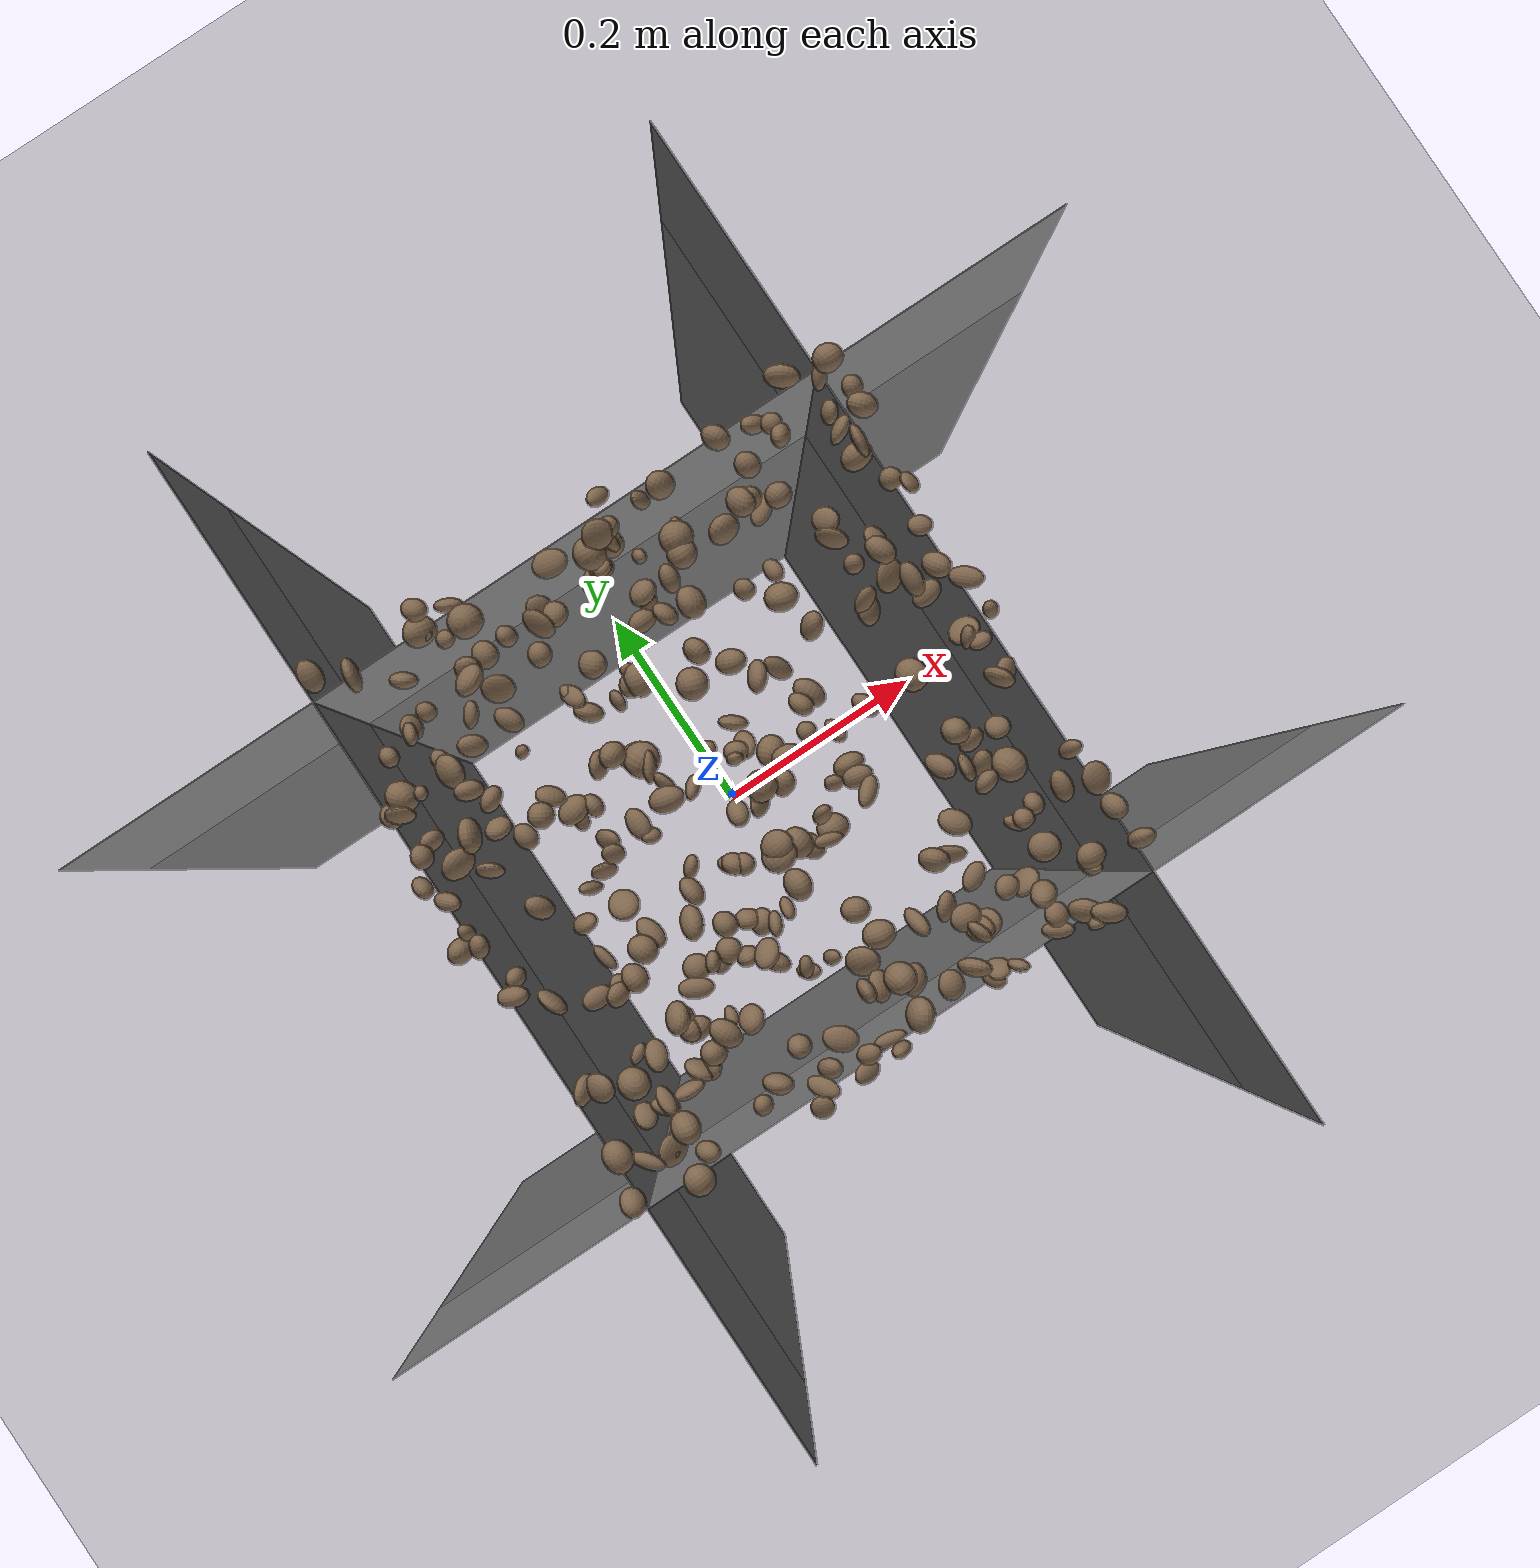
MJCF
<mujoco model="rocky_terrain_scene">

  <default>
    <default class="wall">
      <geom type="plane" size=".5 .5 .05" />
    </default>
  </default>

    <compiler angle="radian" inertiafromgeom="true" />
    <option timestep="0.002" gravity="0 0 -9.81" />

    <worldbody>

        <geom name="+x" class="wall" zaxis="1 0 0" pos="-.25 0 -.25" />
        <geom name="-x" class="wall" zaxis="-1 0 0" pos=".25 0 -.25" />
        <geom name="+y" class="wall" zaxis="0 1 0" pos="0 -.25 -.25" />
        <geom name="-y" class="wall" zaxis="0 -1 0" pos="0 .25 -.25" />

        <light name="sunlight" pos="5 5 5" dir="-1 -1 -1" diffuse="1 1 1" specular="0.5 0.5 0.5" ambient="0.5 0.5 0.5" />

        <geom name="ground_plane" type="plane" size="50 50 0.1" rgba="0.3 0.3 0.3 1" />

        <body name="rocky_terrain_body">

        </body>
    <body name="rock1" pos="-0.15602513288940034 -0.02817647997290429 0.3428036440686796"><joint type="free" /><geom type="ellipsoid" size="0.006503052639317263 0.012969015372331642 0.00895425403588036" quat="0.05615643431479338 0.32436007993347155 0.32823322804936544 0.2912502577023697" rgba="0.5 0.4 0.3 1" /><inertial pos="-0.15602513288940034 -0.02817647997290429 0.3428036440686796" quat="0.05615643431479338 0.32436007993347155 0.32823322804936544 0.2912502577023697" mass="7.5751758543403e-05" /></body><body name="rock2" pos="-0.14692276166876395 -0.08465367928306383 0.34445791441265106"><joint type="free" /><geom type="ellipsoid" size="0.012164190932407608 0.01195223958250126 0.010104714905832134" quat="0.3360681657330323 0.16801916590483135 0.27762727194649967 0.21828539641563677" rgba="0.5 0.4 0.3 1" /><inertial pos="-0.14692276166876395 -0.08465367928306383 0.34445791441265106" quat="0.3360681657330323 0.16801916590483135 0.27762727194649967 0.21828539641563677" mass="4.256784252276608e-05" /></body><body name="rock3" pos="0.2035718366709725 0.05423559195680511 0.34564819771407007"><joint type="free" /><geom type="ellipsoid" size="0.014836706310452405 0.008612702557784922 0.0073107141398401475" quat="0.06379754617663115 0.41065423194578127 0.3399164169769689 0.18563180490061867" rgba="0.5 0.4 0.3 1" /><inertial pos="0.2035718366709725 0.05423559195680511 0.34564819771407007" quat="0.06379754617663115 0.41065423194578127 0.3399164169769689 0.18563180490061867" mass="5.7775010472544356e-05" /></body><body name="rock4" pos="-0.07112566858856967 -0.2025006757266653 0.30607225482106293"><joint type="free" /><geom type="ellipsoid" size="0.009761033457635251 0.01061350159432049 0.008825875502156605" quat="0.18140256044201802 0.09838840380767705 0.24240549461017943 0.4778035411401254" rgba="0.5 0.4 0.3 1" /><inertial pos="-0.07112566858856967 -0.2025006757266653 0.30607225482106293" quat="0.18140256044201802 0.09838840380767705 0.24240549461017943 0.4778035411401254" mass="9.541471732697845e-05" /></body><body name="rock5" pos="0.22989547469456822 0.16712588772407888 0.3455442220154945"><joint type="free" /><geom type="ellipsoid" size="0.014043817993447439 0.014507548804213038 0.005304984494646424" quat="0.295904722698996 0.2409920473476008 0.2170283996394648 0.24607483031393831" rgba="0.5 0.4 0.3 1" /><inertial pos="0.22989547469456822 0.16712588772407888 0.3455442220154945" quat="0.295904722698996 0.2409920473476008 0.2170283996394648 0.24607483031393831" mass="3.843776329502298e-05" /></body><body name="rock6" pos="-0.001500316768458021 -0.0948224283795322 0.32832496625375895"><joint type="free" /><geom type="ellipsoid" size="0.013458769331127867 0.012717454478232509 0.010578967478007174" quat="0.21539274248085077 0.2992142592229782 0.28821037597604143 0.19718262232012967" rgba="0.5 0.4 0.3 1" /><inertial pos="-0.001500316768458021 -0.0948224283795322 0.32832496625375895" quat="0.21539274248085077 0.2992142592229782 0.28821037597604143 0.19718262232012967" mass="9.674941992899901e-05" /></body><body name="rock7" pos="0.016573597184088185 -0.0676628667773031 0.3185423983407274"><joint type="free" /><geom type="ellipsoid" size="0.013740773469626773 0.01166113362637914 0.011777578730105941" quat="0.09938678210230738 0.3494056940678691 0.27722436851141785 0.27398315531840567" rgba="0.5 0.4 0.3 1" /><inertial pos="0.016573597184088185 -0.0676628667773031 0.3185423983407274" quat="0.09938678210230738 0.3494056940678691 0.27722436851141785 0.27398315531840567" mass="4.4553028673208154e-05" /></body><body name="rock8" pos="-0.06641946063557386 0.07051218034317142 0.3270667181572208"><joint type="free" /><geom type="ellipsoid" size="0.011050519362915538 0.01299312223848264 0.01009583295218457" quat="0.40605746952702254 0.38803674100005037 0.005127308393528585 0.2007784810793984" rgba="0.5 0.4 0.3 1" /><inertial pos="-0.06641946063557386 0.07051218034317142 0.3270667181572208" quat="0.40605746952702254 0.38803674100005037 0.005127308393528585 0.2007784810793984" mass="7.419572437092752e-05" /></body><body name="rock9" pos="-0.07528505002308172 -0.10810756599312521 0.31611826828486345"><joint type="free" /><geom type="ellipsoid" size="0.010708294754844567 0.01001647568906582 0.010508472772136452" quat="0.21369832844633194 0.027989352639087122 0.341703847151542 0.41660847176303895" rgba="0.5 0.4 0.3 1" /><inertial pos="-0.07528505002308172 -0.10810756599312521 0.31611826828486345" quat="0.21369832844633194 0.027989352639087122 0.341703847151542 0.41660847176303895" mass="9.064021663134513e-05" /></body><body name="rock10" pos="0.20990082058932047 0.24589901388092877 0.32941528365395484"><joint type="free" /><geom type="ellipsoid" size="0.014669445948880488 0.01136114970525725 0.008499735637656713" quat="0.09451837964129295 0.15203959946341244 0.4330145898429509 0.32042743105234367" rgba="0.5 0.4 0.3 1" /><inertial pos="0.20990082058932047 0.24589901388092877 0.32941528365395484" quat="0.09451837964129295 0.15203959946341244 0.4330145898429509 0.32042743105234367" mass="9.142606207003738e-05" /></body><body name="rock11" pos="0.17699173919805722 -0.07572233408449935 0.30848331794123746"><joint type="free" /><geom type="ellipsoid" size="0.007053026274384847 0.011941694515614502 0.011158603721441836" quat="0.33073775837920527 0.08183237430891298 0.2635941781462983 0.32383568916558353" rgba="0.5 0.4 0.3 1" /><inertial pos="0.17699173919805722 -0.07572233408449935 0.30848331794123746" quat="0.33073775837920527 0.08183237430891298 0.2635941781462983 0.32383568916558353" mass="3.9233677334803014e-05" /></body><body name="rock12" pos="-0.18865468506506305 0.17927913498596182 0.30291883513220635"><joint type="free" /><geom type="ellipsoid" size="0.006215051448926042 0.011063113606970102 0.011390209024882674" quat="0.22594441511536698 0.0350072343967062 0.6031527757693138 0.1358955747186131" rgba="0.5 0.4 0.3 1" /><inertial pos="-0.18865468506506305 0.17927913498596182 0.30291883513220635" quat="0.22594441511536698 0.0350072343967062 0.6031527757693138 0.1358955747186131" mass="5.757047465208739e-05" /></body><body name="rock13" pos="0.00845832134969493 -0.19804773394617275 0.3060192549667395"><joint type="free" /><geom type="ellipsoid" size="0.013403630856647235 0.007633853485279428 0.011430094499267445" quat="0.16075753364943055 0.4286884380137205 0.3017312679488017 0.10882276038804735" rgba="0.5 0.4 0.3 1" /><inertial pos="0.00845832134969493 -0.19804773394617275 0.3060192549667395" quat="0.16075753364943055 0.4286884380137205 0.3017312679488017 0.10882276038804735" mass="5.4382422440969516e-05" /></body><body name="rock14" pos="0.18675676730727153 -0.24580072449692825 0.34447824052548637"><joint type="free" /><geom type="ellipsoid" size="0.008287077954835997 0.014939629515828542 0.008527469086463107" quat="0.5548053940172385 0.011745813465468479 0.13835004311506002 0.295098749402233" rgba="0.5 0.4 0.3 1" /><inertial pos="0.18675676730727153 -0.24580072449692825 0.34447824052548637" quat="0.5548053940172385 0.011745813465468479 0.13835004311506002 0.295098749402233" mass="1.354172785563599e-05" /></body><body name="rock15" pos="-0.1963460800172635 -0.21162506634691786 0.30873916833618087"><joint type="free" /><geom type="ellipsoid" size="0.005443634014047426 0.007011138415884632 0.012034538873232643" quat="0.0468618307175121 0.1687343225635165 0.4943120507086147 0.2900917960103567" rgba="0.5 0.4 0.3 1" /><inertial pos="-0.1963460800172635 -0.21162506634691786 0.30873916833618087" quat="0.0468618307175121 0.1687343225635165 0.4943120507086147 0.2900917960103567" mass="3.5317927142579724e-05" /></body><body name="rock16" pos="-0.12270435456040879 -0.0016574380410483425 0.3151953683638298"><joint type="free" /><geom type="ellipsoid" size="0.005017714920025368 0.01229901909954385 0.01043261277899395" quat="0.36546550965826546 0.16444744709064255 0.23954027168463513 0.23054677156645687" rgba="0.5 0.4 0.3 1" /><inertial pos="-0.12270435456040879 -0.0016574380410483425 0.3151953683638298" quat="0.36546550965826546 0.16444744709064255 0.23954027168463513 0.23054677156645687" mass="9.680489862342004e-05" /></body><body name="rock17" pos="0.1514670172703752 0.20652447699237764 0.30483999649360977"><joint type="free" /><geom type="ellipsoid" size="0.011776799371022311 0.010164977769998397 0.010065673024879557" quat="0.16286692513218262 0.2916503639556086 0.10803579148441736 0.43744691942779135" rgba="0.5 0.4 0.3 1" /><inertial pos="0.1514670172703752 0.20652447699237764 0.30483999649360977" quat="0.16286692513218262 0.2916503639556086 0.10803579148441736 0.43744691942779135" mass="7.391614746692475e-05" /></body><body name="rock18" pos="0.24154700596303036 -0.2126014154969601 0.3360604145747612"><joint type="free" /><geom type="ellipsoid" size="0.01079300059445164 0.007578146936312135 0.012870524557521572" quat="0.12133947014960725 0.12737127822445354 0.059125747158043224 0.692163504467896" rgba="0.5 0.4 0.3 1" /><inertial pos="0.24154700596303036 -0.2126014154969601 0.3360604145747612" quat="0.12133947014960725 0.12737127822445354 0.059125747158043224 0.692163504467896" mass="5.816950407977517e-05" /></body><body name="rock19" pos="0.09048195126962216 -0.010393501352576273 0.3218841600390682"><joint type="free" /><geom type="ellipsoid" size="0.012318909869469504 0.007132786852124885 0.006748779874372278" quat="0.28004187644424106 0.22173566157201785 0.38062174842846835 0.11760071355527259" rgba="0.5 0.4 0.3 1" /><inertial pos="0.09048195126962216 -0.010393501352576273 0.3218841600390682" quat="0.28004187644424106 0.22173566157201785 0.38062174842846835 0.11760071355527259" mass="6.060336733229386e-05" /></body><body name="rock20" pos="-0.06363317789150197 -0.03697060138746472 0.33155024481586476"><joint type="free" /><geom type="ellipsoid" size="0.005737312012411875 0.008287329328833514 0.010305758985146466" quat="0.14517885072522707 0.1414891980543298 0.24222991199264768 0.4711020392277954" rgba="0.5 0.4 0.3 1" /><inertial pos="-0.06363317789150197 -0.03697060138746472 0.33155024481586476" quat="0.14517885072522707 0.1414891980543298 0.24222991199264768 0.4711020392277954" mass="9.733684878382815e-05" /></body><body name="rock21" pos="-0.0405198740616422 -0.21361327288422705 0.3271485430197041"><joint type="free" /><geom type="ellipsoid" size="0.010590790800902502 0.005684826290891421 0.01458761223427284" quat="0.3249006717797174 0.37296300865552107 0.14300032372875668 0.15913599583600493" rgba="0.5 0.4 0.3 1" /><inertial pos="-0.0405198740616422 -0.21361327288422705 0.3271485430197041" quat="0.3249006717797174 0.37296300865552107 0.14300032372875668 0.15913599583600493" mass="8.868815388768e-05" /></body><body name="rock22" pos="0.08119080910301485 0.2245816970552828 0.34395482971347874"><joint type="free" /><geom type="ellipsoid" size="0.009843440918052643 0.014789256287065903 0.011492526036255894" quat="0.2814083530770269 0.10902727302458655 0.30807154390189595 0.30149282999649063" rgba="0.5 0.4 0.3 1" /><inertial pos="0.08119080910301485 0.2245816970552828 0.34395482971347874" quat="0.2814083530770269 0.10902727302458655 0.30807154390189595 0.30149282999649063" mass="9.387124995724708e-05" /></body><body name="rock23" pos="0.19693689110871138 -0.20806287085071296 0.3277079656204638"><joint type="free" /><geom type="ellipsoid" size="0.009310536705963874 0.007978652985505492 0.005920658978733777" quat="0.4077475986296239 0.11087439539012385 0.1875135886634273 0.29386441731682506" rgba="0.5 0.4 0.3 1" /><inertial pos="0.19693689110871138 -0.20806287085071296 0.3277079656204638" quat="0.4077475986296239 0.11087439539012385 0.1875135886634273 0.29386441731682506" mass="2.6150049356858267e-05" /></body><body name="rock24" pos="0.12073633354992336 0.12300793540284316 0.3144249163681756"><joint type="free" /><geom type="ellipsoid" size="0.01095918236672216 0.007651769379078943 0.007373902516145765" quat="0.2291534270991467 0.31472067709877277 0.3872642799526938 0.06886161584938677" rgba="0.5 0.4 0.3 1" /><inertial pos="0.12073633354992336 0.12300793540284316 0.3144249163681756" quat="0.2291534270991467 0.31472067709877277 0.3872642799526938 0.06886161584938677" mass="7.423888245233983e-05" /></body><body name="rock25" pos="-0.10903169194624385 0.24143175827079033 0.32194149762724966"><joint type="free" /><geom type="ellipsoid" size="0.0058286334171294895 0.01096979385867632 0.011763691452895162" quat="0.3188863549877111 0.31098061058655907 0.14129239799407162 0.22884063643165822" rgba="0.5 0.4 0.3 1" /><inertial pos="-0.10903169194624385 0.24143175827079033 0.32194149762724966" quat="0.3188863549877111 0.31098061058655907 0.14129239799407162 0.22884063643165822" mass="1.2587359178610777e-05" /></body><body name="rock26" pos="-0.23777858410662628 0.017241430382134548 0.333685143780673"><joint type="free" /><geom type="ellipsoid" size="0.00645283593225388 0.010758120214614954 0.006328779768637172" quat="0.5618520753840465 0.38010378824656604 0.015101602610636419 0.042942533758751074" rgba="0.5 0.4 0.3 1" /><inertial pos="-0.23777858410662628 0.017241430382134548 0.333685143780673" quat="0.5618520753840465 0.38010378824656604 0.015101602610636419 0.042942533758751074" mass="6.738161381471992e-05" /></body><body name="rock27" pos="-0.11294178035651414 0.16536563582105918 0.31678140869000404"><joint type="free" /><geom type="ellipsoid" size="0.01365839589587935 0.0051091830976649055 0.013493852438342082" quat="0.14781242336815673 0.08950070648227564 0.2337433287518591 0.5289435413977085" rgba="0.5 0.4 0.3 1" /><inertial pos="-0.11294178035651414 0.16536563582105918 0.31678140869000404" quat="0.14781242336815673 0.08950070648227564 0.2337433287518591 0.5289435413977085" mass="7.216859058890899e-05" /></body><body name="rock28" pos="0.02989093301686807 -0.16259025062666266 0.32187841492622454"><joint type="free" /><geom type="ellipsoid" size="0.011422086981479694 0.011690339686661805 0.013456764008810192" quat="0.23332060961375353 0.3158443281637013 0.15710491538392202 0.29373014683862314" rgba="0.5 0.4 0.3 1" /><inertial pos="0.02989093301686807 -0.16259025062666266 0.32187841492622454" quat="0.23332060961375353 0.3158443281637013 0.15710491538392202 0.29373014683862314" mass="9.257843062887806e-05" /></body><body name="rock29" pos="0.0853295500086863 -0.05020857823294661 0.3158455283951889"><joint type="free" /><geom type="ellipsoid" size="0.009515724709748947 0.008874112628454226 0.012726219974072299" quat="0.1990398601426821 0.330735391628974 0.09340694092238012 0.37681780730596376" rgba="0.5 0.4 0.3 1" /><inertial pos="0.0853295500086863 -0.05020857823294661 0.3158455283951889" quat="0.1990398601426821 0.330735391628974 0.09340694092238012 0.37681780730596376" mass="4.185165180584125e-05" /></body><body name="rock30" pos="-0.20594805151560952 0.1263324143724715 0.348974767318203"><joint type="free" /><geom type="ellipsoid" size="0.005284198402440651 0.006153445758894618 0.005956691971002682" quat="0.15267495507195483 0.14146950120308865 0.004481405522081907 0.7013741382028746" rgba="0.5 0.4 0.3 1" /><inertial pos="-0.20594805151560952 0.1263324143724715 0.348974767318203" quat="0.15267495507195483 0.14146950120308865 0.004481405522081907 0.7013741382028746" mass="6.104133781616966e-05" /></body><body name="rock31" pos="-0.19909195121681933 -0.21444726777718254 0.3125499606916338"><joint type="free" /><geom type="ellipsoid" size="0.0055180945328777474 0.014671562619639159 0.013797834918950657" quat="0.29167389331809285 0.060299441069999904 0.42348256845736054 0.22454409715454668" rgba="0.5 0.4 0.3 1" /><inertial pos="-0.19909195121681933 -0.21444726777718254 0.3125499606916338" quat="0.29167389331809285 0.060299441069999904 0.42348256845736054 0.22454409715454668" mass="1.2412493108383501e-05" /></body><body name="rock32" pos="-0.0706614520090681 0.16997588742247188 0.3153597991367486"><joint type="free" /><geom type="ellipsoid" size="0.009449786954726681 0.010434247446600233 0.00990639694641709" quat="0.10564827254067308 0.1737140332733088 0.032617874245799545 0.6880198199402184" rgba="0.5 0.4 0.3 1" /><inertial pos="-0.0706614520090681 0.16997588742247188 0.3153597991367486" quat="0.10564827254067308 0.1737140332733088 0.032617874245799545 0.6880198199402184" mass="6.063911366421924e-05" /></body><body name="rock33" pos="0.1882172253343143 -0.10787264733101903 0.33309473457551475"><joint type="free" /><geom type="ellipsoid" size="0.014695785571467883 0.012144268208430082 0.01407912834257256" quat="0.14522603415927351 0.29016329619260195 0.3892271613016308 0.17538350834649363" rgba="0.5 0.4 0.3 1" /><inertial pos="0.1882172253343143 -0.10787264733101903 0.33309473457551475" quat="0.14522603415927351 0.29016329619260195 0.3892271613016308 0.17538350834649363" mass="3.3265883713458416e-05" /></body><body name="rock34" pos="-0.18122730632083361 -0.13685488986154504 0.30139462183077587"><joint type="free" /><geom type="ellipsoid" size="0.005041601103896979 0.00500794821616153 0.00910342553654516" quat="0.20674136398119813 0.14245029584279503 0.3501653711086666 0.30064296906734017" rgba="0.5 0.4 0.3 1" /><inertial pos="-0.18122730632083361 -0.13685488986154504 0.30139462183077587" quat="0.20674136398119813 0.14245029584279503 0.3501653711086666 0.30064296906734017" mass="5.292691720424232e-05" /></body><body name="rock35" pos="-0.1646559254678997 -0.08828810956651006 0.3449416842810355"><joint type="free" /><geom type="ellipsoid" size="0.010511714628069015 0.01077505506649043 0.007446664402952869" quat="0.47851789182083976 0.29642887597004614 0.02154768947034904 0.20350554273876512" rgba="0.5 0.4 0.3 1" /><inertial pos="-0.1646559254678997 -0.08828810956651006 0.3449416842810355" quat="0.47851789182083976 0.29642887597004614 0.02154768947034904 0.20350554273876512" mass="3.78537434730408e-05" /></body><body name="rock36" pos="-0.23482084997520547 -0.0443109817178039 0.33518689421741704"><joint type="free" /><geom type="ellipsoid" size="0.008274057223268398 0.009675406500541182 0.01325573490841906" quat="0.32041636942949064 0.2739994056906192 0.11436254864883416 0.29122167623105594" rgba="0.5 0.4 0.3 1" /><inertial pos="-0.23482084997520547 -0.0443109817178039 0.33518689421741704" quat="0.32041636942949064 0.2739994056906192 0.11436254864883416 0.29122167623105594" mass="7.696684949556696e-05" /></body><body name="rock37" pos="0.024483820516590926 -0.07509221429943608 0.3037712742829304"><joint type="free" /><geom type="ellipsoid" size="0.013956688193193848 0.006665147162548532 0.009735156204127831" quat="0.1125268116267714 0.2543294566361197 0.3203078187783864 0.3128359129587226" rgba="0.5 0.4 0.3 1" /><inertial pos="0.024483820516590926 -0.07509221429943608 0.3037712742829304" quat="0.1125268116267714 0.2543294566361197 0.3203078187783864 0.3128359129587226" mass="7.690438571283814e-05" /></body><body name="rock38" pos="-0.23350067593669832 0.08550341298233899 0.33899033742760104"><joint type="free" /><geom type="ellipsoid" size="0.010156298011764747 0.009904849781194273 0.008431574302275728" quat="0.3913519849537769 0.19071933183958525 0.15371182561154154 0.26421685759509633" rgba="0.5 0.4 0.3 1" /><inertial pos="-0.23350067593669832 0.08550341298233899 0.33899033742760104" quat="0.3913519849537769 0.19071933183958525 0.15371182561154154 0.26421685759509633" mass="8.558223848470453e-05" /></body><body name="rock39" pos="0.23783118023552963 -0.18036045277755675 0.3346927074156925"><joint type="free" /><geom type="ellipsoid" size="0.0116512871888792 0.008726834270364416 0.009389505361805852" quat="0.3218306490141112 0.09437600071851157 0.25898112263995887 0.3248122276274184" rgba="0.5 0.4 0.3 1" /><inertial pos="0.23783118023552963 -0.18036045277755675 0.3346927074156925" quat="0.3218306490141112 0.09437600071851157 0.25898112263995887 0.3248122276274184" mass="3.326500826537259e-05" /></body><body name="rock40" pos="0.07731049997672024 -0.2245709807315623 0.33424801769915546"><joint type="free" /><geom type="ellipsoid" size="0.013831137042554658 0.011913867116667521 0.0071130696090633124" quat="0.20477460957719276 0.07614162967337752 0.4189549052380151 0.30012885551141466" rgba="0.5 0.4 0.3 1" /><inertial pos="0.07731049997672024 -0.2245709807315623 0.33424801769915546" quat="0.20477460957719276 0.07614162967337752 0.4189549052380151 0.30012885551141466" mass="1.0021961847885857e-05" /></body><body name="rock41" pos="0.10689278336847796 0.1738460407310537 0.30441832569587657"><joint type="free" /><geom type="ellipsoid" size="0.009104168017282149 0.014962371505743075 0.013272482073563269" quat="0.31067696291314 0.08627430642940709 0.2849643978428884 0.3180843328145645" rgba="0.5 0.4 0.3 1" /><inertial pos="0.10689278336847796 0.1738460407310537 0.30441832569587657" quat="0.31067696291314 0.08627430642940709 0.2849643978428884 0.3180843328145645" mass="3.4718373719519505e-05" /></body><body name="rock42" pos="0.024877348865400217 0.21282588752085413 0.3102563974581353"><joint type="free" /><geom type="ellipsoid" size="0.010558894148542577 0.013880021069185858 0.007992772286662182" quat="0.10013178334582631 0.19189003943893868 0.45530141894235787 0.25267675827287717" rgba="0.5 0.4 0.3 1" /><inertial pos="0.024877348865400217 0.21282588752085413 0.3102563974581353" quat="0.10013178334582631 0.19189003943893868 0.45530141894235787 0.25267675827287717" mass="8.269407535755023e-05" /></body><body name="rock43" pos="-0.019371310773691086 0.11040606765524369 0.30745043545090944"><joint type="free" /><geom type="ellipsoid" size="0.011330696205828068 0.012877749895982192 0.01461266389483682" quat="0.20743297272064098 0.2667079541015216 0.23019675229350467 0.2956623208843328" rgba="0.5 0.4 0.3 1" /><inertial pos="-0.019371310773691086 0.11040606765524369 0.30745043545090944" quat="0.20743297272064098 0.2667079541015216 0.23019675229350467 0.2956623208843328" mass="7.639616053547636e-05" /></body><body name="rock44" pos="-0.12651807529200637 0.22233671139937272 0.311754368595689"><joint type="free" /><geom type="ellipsoid" size="0.008372055537767268 0.0066802264195208495 0.007471695713594191" quat="0.25889678024513246 0.009919832941331022 0.41977529279273657 0.31140809402079994" rgba="0.5 0.4 0.3 1" /><inertial pos="-0.12651807529200637 0.22233671139937272 0.311754368595689" quat="0.25889678024513246 0.009919832941331022 0.41977529279273657 0.31140809402079994" mass="1.4908355865974538e-05" /></body><body name="rock45" pos="0.019138293858234234 0.21907972609384202 0.34479954186704126"><joint type="free" /><geom type="ellipsoid" size="0.013527661781957218 0.005817867205697322 0.0127990119731687" quat="0.2293698062456591 0.429950160844667 0.09188583347928511 0.2487941994303887" rgba="0.5 0.4 0.3 1" /><inertial pos="0.019138293858234234 0.21907972609384202 0.34479954186704126" quat="0.2293698062456591 0.429950160844667 0.09188583347928511 0.2487941994303887" mass="5.518231838696255e-05" /></body><body name="rock46" pos="-0.1383341751440586 0.06076200458086667 0.3417894836186489"><joint type="free" /><geom type="ellipsoid" size="0.010615257931384715 0.011378556856135535 0.010625467529810612" quat="0.22289799292785398 0.021643613717632328 0.3748679875766272 0.3805904057778865" rgba="0.5 0.4 0.3 1" /><inertial pos="-0.1383341751440586 0.06076200458086667 0.3417894836186489" quat="0.22289799292785398 0.021643613717632328 0.3748679875766272 0.3805904057778865" mass="3.5230467504361266e-05" /></body><body name="rock47" pos="-0.13225261746547073 0.24914179261387548 0.34355056902364123"><joint type="free" /><geom type="ellipsoid" size="0.008714070834476693 0.011153036094016567 0.00969220398800254" quat="0.06364386504834864 0.49750992160643454 0.17939698882632432 0.2594492245188926" rgba="0.5 0.4 0.3 1" /><inertial pos="-0.13225261746547073 0.24914179261387548 0.34355056902364123" quat="0.06364386504834864 0.49750992160643454 0.17939698882632432 0.2594492245188926" mass="8.939128798975238e-05" /></body><body name="rock48" pos="0.17757862537624108 -0.24874749763384024 0.33277723959253913"><joint type="free" /><geom type="ellipsoid" size="0.00864956137935881 0.005133948059457213 0.009261495292539765" quat="0.23652398974686425 0.04531042861647181 0.6791501678534215 0.03901541378324248" rgba="0.5 0.4 0.3 1" /><inertial pos="0.17757862537624108 -0.24874749763384024 0.33277723959253913" quat="0.23652398974686425 0.04531042861647181 0.6791501678534215 0.03901541378324248" mass="4.740534139559159e-05" /></body><body name="rock49" pos="0.024322913952729897 -0.19914913594332923 0.3346324593199033"><joint type="free" /><geom type="ellipsoid" size="0.014143217731559132 0.012146934319664706 0.012744146217855067" quat="0.34706409997488175 0.09782825582085414 0.4048788494156271 0.1502287947886371" rgba="0.5 0.4 0.3 1" /><inertial pos="0.024322913952729897 -0.19914913594332923 0.3346324593199033" quat="0.34706409997488175 0.09782825582085414 0.4048788494156271 0.1502287947886371" mass="4.160887555319108e-05" /></body><body name="rock50" pos="-0.21716534201322907 0.06799432700450458 0.3046961023002056"><joint type="free" /><geom type="ellipsoid" size="0.008713135111853745 0.014523310227889701 0.01475630616808159" quat="0.3245960322702254 0.1027383629320667 0.323280024824263 0.24938557997344496" rgba="0.5 0.4 0.3 1" /><inertial pos="-0.21716534201322907 0.06799432700450458 0.3046961023002056" quat="0.3245960322702254 0.1027383629320667 0.323280024824263 0.24938557997344496" mass="7.016155143748211e-05" /></body><body name="rock51" pos="-0.1316805516142771 -0.06996281542521599 0.3119949842799582"><joint type="free" /><geom type="ellipsoid" size="0.012726584285446147 0.011660556240139376 0.011262254075379598" quat="0.23162850820967767 0.16619273506081528 0.1640578542762077 0.4381209024532993" rgba="0.5 0.4 0.3 1" /><inertial pos="-0.1316805516142771 -0.06996281542521599 0.3119949842799582" quat="0.23162850820967767 0.16619273506081528 0.1640578542762077 0.4381209024532993" mass="8.498149017748003e-05" /></body><body name="rock52" pos="0.054122925091337704 -0.22497293318063394 0.34127683831816497"><joint type="free" /><geom type="ellipsoid" size="0.012251799762818408 0.007257994967725482 0.010795948084784356" quat="0.21243694352355963 0.3603654132790329 0.2272733028553586 0.199924340342049" rgba="0.5 0.4 0.3 1" /><inertial pos="0.054122925091337704 -0.22497293318063394 0.34127683831816497" quat="0.21243694352355963 0.3603654132790329 0.2272733028553586 0.199924340342049" mass="5.186025387485392e-05" /></body><body name="rock53" pos="-0.07305611475761026 -0.24048361059258627 0.3052910494213901"><joint type="free" /><geom type="ellipsoid" size="0.008327727205424164 0.01458201938491676 0.005711947967185921" quat="0.09683685044455875 0.663835941200161 0.20842042921236087 0.030906779142919432" rgba="0.5 0.4 0.3 1" /><inertial pos="-0.07305611475761026 -0.24048361059258627 0.3052910494213901" quat="0.09683685044455875 0.663835941200161 0.20842042921236087 0.030906779142919432" mass="7.082340156206051e-05" /></body><body name="rock54" pos="0.0687981592973349 0.18290335344768677 0.3474975486232418"><joint type="free" /><geom type="ellipsoid" size="0.013044433197302929 0.014106958289282653 0.01317976865804477" quat="0.34113132103121135 0.19415556491929692 0.0849541722956071 0.3797589417538846" rgba="0.5 0.4 0.3 1" /><inertial pos="0.0687981592973349 0.18290335344768677 0.3474975486232418" quat="0.34113132103121135 0.19415556491929692 0.0849541722956071 0.3797589417538846" mass="8.584638094873098e-05" /></body><body name="rock55" pos="-0.23190964146811544 -0.1365807892706805 0.310995783609391"><joint type="free" /><geom type="ellipsoid" size="0.013952629227485969 0.01234846991682029 0.007070990567967932" quat="0.4639556003791213 0.26240068252289506 0.24076081365198787 0.03288290344599576" rgba="0.5 0.4 0.3 1" /><inertial pos="-0.23190964146811544 -0.1365807892706805 0.310995783609391" quat="0.4639556003791213 0.26240068252289506 0.24076081365198787 0.03288290344599576" mass="9.667258840227504e-05" /></body><body name="rock56" pos="0.1729351838631975 0.08955770465588203 0.3424500498351296"><joint type="free" /><geom type="ellipsoid" size="0.007270036127111745 0.00909691767667202 0.008123963139323806" quat="0.3754962936375531 0.24976938523518394 0.2767595362397458 0.09797478488751721" rgba="0.5 0.4 0.3 1" /><inertial pos="0.1729351838631975 0.08955770465588203 0.3424500498351296" quat="0.3754962936375531 0.24976938523518394 0.2767595362397458 0.09797478488751721" mass="7.291985626970764e-05" /></body><body name="rock57" pos="-0.08794479703894553 -0.07396096585670558 0.31108357564641"><joint type="free" /><geom type="ellipsoid" size="0.014865787851998654 0.009166777626391176 0.011738851249065577" quat="0.49477094504454183 0.02813427847970363 0.15848031180227787 0.3186144646734767" rgba="0.5 0.4 0.3 1" /><inertial pos="-0.08794479703894553 -0.07396096585670558 0.31108357564641" quat="0.49477094504454183 0.02813427847970363 0.15848031180227787 0.3186144646734767" mass="8.844607017372944e-05" /></body><body name="rock58" pos="0.022673549915477653 -0.23559332998963656 0.30194983258286257"><joint type="free" /><geom type="ellipsoid" size="0.014691898845926823 0.014925204466683505 0.010747524014280863" quat="0.301417926203914 0.300422150008373 0.3358862078360136 0.06227371595169946" rgba="0.5 0.4 0.3 1" /><inertial pos="0.022673549915477653 -0.23559332998963656 0.30194983258286257" quat="0.301417926203914 0.300422150008373 0.3358862078360136 0.06227371595169946" mass="5.571839818551201e-05" /></body><body name="rock59" pos="-0.04109605410537659 -0.10417493548635037 0.3065657481967762"><joint type="free" /><geom type="ellipsoid" size="0.011389708334680917 0.010301872005218083 0.008855626307341009" quat="0.17357279119603997 0.4834056064171621 0.16020228623685961 0.1828193161499383" rgba="0.5 0.4 0.3 1" /><inertial pos="-0.04109605410537659 -0.10417493548635037 0.3065657481967762" quat="0.17357279119603997 0.4834056064171621 0.16020228623685961 0.1828193161499383" mass="3.9250292457452467e-05" /></body><body name="rock60" pos="-0.22173513858036892 0.09255139923856515 0.3299485183647627"><joint type="free" /><geom type="ellipsoid" size="0.007299100619327663 0.01174980075711672 0.010142633299576704" quat="0.2944897911287521 0.12305337799578643 0.24935482530006867 0.3331020055753927" rgba="0.5 0.4 0.3 1" /><inertial pos="-0.22173513858036892 0.09255139923856515 0.3299485183647627" quat="0.2944897911287521 0.12305337799578643 0.24935482530006867 0.3331020055753927" mass="7.751031576285802e-05" /></body><body name="rock61" pos="-0.11788255248910662 0.13680555034274272 0.343896869052905"><joint type="free" /><geom type="ellipsoid" size="0.01259204905117467 0.007515254533391635 0.008972241698773607" quat="0.23698825249937272 0.14804529757138302 0.21255771820255454 0.4024087317266897" rgba="0.5 0.4 0.3 1" /><inertial pos="-0.11788255248910662 0.13680555034274272 0.343896869052905" quat="0.23698825249937272 0.14804529757138302 0.21255771820255454 0.4024087317266897" mass="2.7709088765076712e-05" /></body><body name="rock62" pos="0.18128962962547546 0.2054137899137925 0.3429966292691072"><joint type="free" /><geom type="ellipsoid" size="0.007717454596105839 0.014120973334697647 0.009329437591338103" quat="0.15194123855052996 0.041543914448582006 0.30728557783119337 0.4992292691696947" rgba="0.5 0.4 0.3 1" /><inertial pos="0.18128962962547546 0.2054137899137925 0.3429966292691072" quat="0.15194123855052996 0.041543914448582006 0.30728557783119337 0.4992292691696947" mass="5.73648800257099e-05" /></body><body name="rock63" pos="0.18060025156212484 0.21726530905158076 0.34229855497124506"><joint type="free" /><geom type="ellipsoid" size="0.008461257727655117 0.006973152511389559 0.008567234130962522" quat="0.30533757450239385 0.2405675016607147 0.21783456993824932 0.23626035389864217" rgba="0.5 0.4 0.3 1" /><inertial pos="0.18060025156212484 0.21726530905158076 0.34229855497124506" quat="0.30533757450239385 0.2405675016607147 0.21783456993824932 0.23626035389864217" mass="4.659953367128848e-05" /></body><body name="rock64" pos="-0.002877667226854508 -0.19363334995117537 0.32569105841461343"><joint type="free" /><geom type="ellipsoid" size="0.010139489886270248 0.013558956195096242 0.006473346827353519" quat="0.23808302030509515 0.2733713028413263 0.22396936090735273 0.26457631594622577" rgba="0.5 0.4 0.3 1" /><inertial pos="-0.002877667226854508 -0.19363334995117537 0.32569105841461343" quat="0.23808302030509515 0.2733713028413263 0.22396936090735273 0.26457631594622577" mass="2.7426232712228683e-05" /></body><body name="rock65" pos="0.03799167839261752 -0.0789285856031301 0.3273592291108521"><joint type="free" /><geom type="ellipsoid" size="0.00564577729329307 0.005780869972631315 0.012339231047882915" quat="0.24683374107853287 0.3325054622229434 0.23263380618711155 0.1880269905114122" rgba="0.5 0.4 0.3 1" /><inertial pos="0.03799167839261752 -0.0789285856031301 0.3273592291108521" quat="0.24683374107853287 0.3325054622229434 0.23263380618711155 0.1880269905114122" mass="8.746128288803684e-05" /></body><body name="rock66" pos="0.11576622694970712 -0.16496683869320633 0.338356132979954"><joint type="free" /><geom type="ellipsoid" size="0.007972526561296676 0.0057305448201368245 0.012585683186220678" quat="0.15243753395491147 0.221591643329031 0.3097151531438999 0.3162556695721577" rgba="0.5 0.4 0.3 1" /><inertial pos="0.11576622694970712 -0.16496683869320633 0.338356132979954" quat="0.15243753395491147 0.221591643329031 0.3097151531438999 0.3162556695721577" mass="5.9823721321473586e-05" /></body><body name="rock67" pos="0.09536102602438723 -0.20308641312301257 0.34034120590346545"><joint type="free" /><geom type="ellipsoid" size="0.005426456387445459 0.009170149118285748 0.011443712639230897" quat="0.3819591982222348 0.46762280426276903 0.09077451305438898 0.059643484460607174" rgba="0.5 0.4 0.3 1" /><inertial pos="0.09536102602438723 -0.20308641312301257 0.34034120590346545" quat="0.3819591982222348 0.46762280426276903 0.09077451305438898 0.059643484460607174" mass="7.004130059416772e-05" /></body><body name="rock68" pos="-0.1267205766656932 0.1798084854685995 0.34303858713057844"><joint type="free" /><geom type="ellipsoid" size="0.008556417104614609 0.012684297167065723 0.013987641242843175" quat="0.07348433609331848 0.3034794409966604 0.2960011185243347 0.32703510438568645" rgba="0.5 0.4 0.3 1" /><inertial pos="-0.1267205766656932 0.1798084854685995 0.34303858713057844" quat="0.07348433609331848 0.3034794409966604 0.2960011185243347 0.32703510438568645" mass="9.387848480833505e-05" /></body><body name="rock69" pos="-0.20113522022414482 0.23404982379298617 0.34119633545915945"><joint type="free" /><geom type="ellipsoid" size="0.006294121077421104 0.013717864616466149 0.014815846064131832" quat="0.06673848023901457 0.030338800851225683 0.22701575010460354 0.6759069688051562" rgba="0.5 0.4 0.3 1" /><inertial pos="-0.20113522022414482 0.23404982379298617 0.34119633545915945" quat="0.06673848023901457 0.030338800851225683 0.22701575010460354 0.6759069688051562" mass="5.642279917950153e-05" /></body><body name="rock70" pos="-0.1242890976191387 0.06953946123144444 0.33357978269561417"><joint type="free" /><geom type="ellipsoid" size="0.009426734990156876 0.006603038022450021 0.012817236040620402" quat="0.306064646818499 0.3354899565309234 0.32839004642071495 0.03005535022986271" rgba="0.5 0.4 0.3 1" /><inertial pos="-0.1242890976191387 0.06953946123144444 0.33357978269561417" quat="0.306064646818499 0.3354899565309234 0.32839004642071495 0.03005535022986271" mass="2.6863074208717117e-05" /></body><body name="rock71" pos="-0.10072971830690391 -0.21613661106310056 0.3218234429646398"><joint type="free" /><geom type="ellipsoid" size="0.008088152558716722 0.012194988788741729 0.012659241889949747" quat="0.4794096450841696 0.22106034241773143 0.05494431627942183 0.2445856962186771" rgba="0.5 0.4 0.3 1" /><inertial pos="-0.10072971830690391 -0.21613661106310056 0.3218234429646398" quat="0.4794096450841696 0.22106034241773143 0.05494431627942183 0.2445856962186771" mass="6.507094113981482e-05" /></body><body name="rock72" pos="-0.17148175361081863 0.2120705168703656 0.318160141837455"><joint type="free" /><geom type="ellipsoid" size="0.011453404853680238 0.01251114970147856 0.006644153161230476" quat="0.011512041690804407 0.2187495354434206 0.3166189529254956 0.45311946994027935" rgba="0.5 0.4 0.3 1" /><inertial pos="-0.17148175361081863 0.2120705168703656 0.318160141837455" quat="0.011512041690804407 0.2187495354434206 0.3166189529254956 0.45311946994027935" mass="3.236588537228415e-05" /></body><body name="rock73" pos="0.0780512213128724 0.021120378860897737 0.3441078677536117"><joint type="free" /><geom type="ellipsoid" size="0.010976657580911483 0.009990724341074309 0.007820340195230363" quat="0.309044481027768 0.10631443416945635 0.2658105246588545 0.3188305601439212" rgba="0.5 0.4 0.3 1" /><inertial pos="0.0780512213128724 0.021120378860897737 0.3441078677536117" quat="0.309044481027768 0.10631443416945635 0.2658105246588545 0.3188305601439212" mass="4.986314643044378e-05" /></body><body name="rock74" pos="-0.037815159537680276 -0.24960252036371905 0.30689035111057683"><joint type="free" /><geom type="ellipsoid" size="0.00867934974703216 0.005206443200219652 0.012230376072153508" quat="0.16436036563415185 0.37712407776334916 0.2487465697279262 0.2097689868745728" rgba="0.5 0.4 0.3 1" /><inertial pos="-0.037815159537680276 -0.24960252036371905 0.30689035111057683" quat="0.16436036563415185 0.37712407776334916 0.2487465697279262 0.2097689868745728" mass="2.886758771107589e-05" /></body><body name="rock75" pos="0.23685922324472986 0.23184055201141957 0.32045162071429284"><joint type="free" /><geom type="ellipsoid" size="0.01269027491274884 0.0059723006786929385 0.00621196047659614" quat="0.12617879000982687 0.48284163274302605 0.19971756084366266 0.1912620164034844" rgba="0.5 0.4 0.3 1" /><inertial pos="0.23685922324472986 0.23184055201141957 0.32045162071429284" quat="0.12617879000982687 0.48284163274302605 0.19971756084366266 0.1912620164034844" mass="4.105696477931399e-05" /></body><body name="rock76" pos="-0.10669564531208259 0.19295251004063196 0.32128163957102135"><joint type="free" /><geom type="ellipsoid" size="0.010668190869105946 0.011533934839577334 0.010128525640847694" quat="0.040361550752671796 0.7008398972013669 0.020406845457542153 0.2383917065884192" rgba="0.5 0.4 0.3 1" /><inertial pos="-0.10669564531208259 0.19295251004063196 0.32128163957102135" quat="0.040361550752671796 0.7008398972013669 0.020406845457542153 0.2383917065884192" mass="4.687756995154655e-05" /></body><body name="rock77" pos="-0.15714802967948305 0.05383685571177321 0.34058542679482157"><joint type="free" /><geom type="ellipsoid" size="0.011313450240664009 0.008954223581386745 0.00887444250609079" quat="0.03312761248029007 0.3957710295197475 0.4658518181497623 0.10524953985020012" rgba="0.5 0.4 0.3 1" /><inertial pos="-0.15714802967948305 0.05383685571177321 0.34058542679482157" quat="0.03312761248029007 0.3957710295197475 0.4658518181497623 0.10524953985020012" mass="3.2212137281262105e-05" /></body><body name="rock78" pos="0.07334160041682442 0.19087340476560982 0.3357478901299683"><joint type="free" /><geom type="ellipsoid" size="0.008972984232578095 0.007258397093119052 0.005673467215492351" quat="0.2713293876424052 0.3593926303041175 0.09464380186278236 0.27463418019069497" rgba="0.5 0.4 0.3 1" /><inertial pos="0.07334160041682442 0.19087340476560982 0.3357478901299683" quat="0.2713293876424052 0.3593926303041175 0.09464380186278236 0.27463418019069497" mass="2.3651010513695838e-05" /></body><body name="rock79" pos="-0.08128427808078875 -0.11103600836006733 0.30263399435900074"><joint type="free" /><geom type="ellipsoid" size="0.01476152951631917 0.006021607533575321 0.008255762385655832" quat="0.36857053746511287 0.3937207504256387 0.09536172226529267 0.1423469898439558" rgba="0.5 0.4 0.3 1" /><inertial pos="-0.08128427808078875 -0.11103600836006733 0.30263399435900074" quat="0.36857053746511287 0.3937207504256387 0.09536172226529267 0.1423469898439558" mass="1.5616689550545834e-05" /></body><body name="rock80" pos="-0.17378374342235298 0.10742193204564576 0.34940020600681204"><joint type="free" /><geom type="ellipsoid" size="0.012152946197568557 0.0079797031468787 0.009739638143376186" quat="0.116160438854173 0.15640217081179317 0.03324472328765115 0.6941926670463827" rgba="0.5 0.4 0.3 1" /><inertial pos="-0.17378374342235298 0.10742193204564576 0.34940020600681204" quat="0.116160438854173 0.15640217081179317 0.03324472328765115 0.6941926670463827" mass="9.468260016472727e-05" /></body><body name="rock81" pos="-0.0056041123850138486 -0.24542776811318273 0.34045697236448574"><joint type="free" /><geom type="ellipsoid" size="0.006097859547534562 0.013475275479957843 0.007527191003769758" quat="0.31548706346516514 0.23101801840153582 0.1675464635539264 0.2859484545793726" rgba="0.5 0.4 0.3 1" /><inertial pos="-0.0056041123850138486 -0.24542776811318273 0.34045697236448574" quat="0.31548706346516514 0.23101801840153582 0.1675464635539264 0.2859484545793726" mass="4.5405759878084856e-05" /></body><body name="rock82" pos="0.14853124596618716 -0.2374570330589736 0.3254751788069683"><joint type="free" /><geom type="ellipsoid" size="0.006832189904065569 0.0063173927249000235 0.0128684815324542" quat="0.2837611709449993 0.3415023708633574 0.06845352336560377 0.30628293482603947" rgba="0.5 0.4 0.3 1" /><inertial pos="0.14853124596618716 -0.2374570330589736 0.3254751788069683" quat="0.2837611709449993 0.3415023708633574 0.06845352336560377 0.30628293482603947" mass="3.303384663725635e-05" /></body><body name="rock83" pos="0.05097083177642103 0.13531647901361632 0.33882870248287045"><joint type="free" /><geom type="ellipsoid" size="0.013591285933884357 0.010660459343179753 0.013577937720168996" quat="0.11708082678555687 0.4413385371072579 0.3806906095523361 0.0608900265548492" rgba="0.5 0.4 0.3 1" /><inertial pos="0.05097083177642103 0.13531647901361632 0.33882870248287045" quat="0.11708082678555687 0.4413385371072579 0.3806906095523361 0.0608900265548492" mass="8.553948533807693e-05" /></body><body name="rock84" pos="-0.028061201234931832 0.013484522846128666 0.34640558745031597"><joint type="free" /><geom type="ellipsoid" size="0.005869888314691619 0.01332537079925987 0.007675715525611212" quat="0.1976679565040772 0.10550546008439488 0.21319183027790706 0.48363475313362086" rgba="0.5 0.4 0.3 1" /><inertial pos="-0.028061201234931832 0.013484522846128666 0.34640558745031597" quat="0.1976679565040772 0.10550546008439488 0.21319183027790706 0.48363475313362086" mass="5.3356244794077745e-05" /></body><body name="rock85" pos="-0.11261106430492024 -0.11813933595143672 0.3270868541318307"><joint type="free" /><geom type="ellipsoid" size="0.014383411220495176 0.008654544319781587 0.0063252706646766705" quat="0.01648500498423893 0.18881306815415766 0.7479747615812672 0.04672716528033621" rgba="0.5 0.4 0.3 1" /><inertial pos="-0.11261106430492024 -0.11813933595143672 0.3270868541318307" quat="0.01648500498423893 0.18881306815415766 0.7479747615812672 0.04672716528033621" mass="1.6145282150322995e-05" /></body><body name="rock86" pos="-0.24982601230303847 0.008098068471039388 0.3282108080061763"><joint type="free" /><geom type="ellipsoid" size="0.009705041744340979 0.012027367903025367 0.014792899317922343" quat="0.043242305138675996 0.39780908255338665 0.5395086542866259 0.019439958021311453" rgba="0.5 0.4 0.3 1" /><inertial pos="-0.24982601230303847 0.008098068471039388 0.3282108080061763" quat="0.043242305138675996 0.39780908255338665 0.5395086542866259 0.019439958021311453" mass="6.265645663394045e-05" /></body><body name="rock87" pos="0.0935349951164613 -0.1887367269625682 0.328040740183059"><joint type="free" /><geom type="ellipsoid" size="0.00751423244813932 0.010963935101386522 0.012672661425809258" quat="0.455717818147295 0.046516697708271756 0.4907180512551081 0.007047432889325167" rgba="0.5 0.4 0.3 1" /><inertial pos="0.0935349951164613 -0.1887367269625682 0.328040740183059" quat="0.455717818147295 0.046516697708271756 0.4907180512551081 0.007047432889325167" mass="5.3917425821794965e-05" /></body><body name="rock88" pos="0.1532522169585928 -0.22534086873067855 0.3353237510867686"><joint type="free" /><geom type="ellipsoid" size="0.01017549129056659 0.007856547377467887 0.0104995351364492" quat="0.12372704375910225 0.31007432992604 0.33923703159057583 0.22696159472428196" rgba="0.5 0.4 0.3 1" /><inertial pos="0.1532522169585928 -0.22534086873067855 0.3353237510867686" quat="0.12372704375910225 0.31007432992604 0.33923703159057583 0.22696159472428196" mass="9.761023465280958e-05" /></body><body name="rock89" pos="-0.10775641662238006 0.004557241049676142 0.3454120542322414"><joint type="free" /><geom type="ellipsoid" size="0.01070169060601498 0.005870626384537421 0.008840260732152983" quat="0.145282166928613 0.3233425925381469 0.11584548867694781 0.41552975185629215" rgba="0.5 0.4 0.3 1" /><inertial pos="-0.10775641662238006 0.004557241049676142 0.3454120542322414" quat="0.145282166928613 0.3233425925381469 0.11584548867694781 0.41552975185629215" mass="2.7713225219388173e-05" /></body><body name="rock90" pos="0.17376257839796672 -0.14902033894975292 0.33427780035290444"><joint type="free" /><geom type="ellipsoid" size="0.008691594112459467 0.007368180383110071 0.008597728686043433" quat="0.3380383392286998 0.31186948880851784 0.28030810020469316 0.06978407175808929" rgba="0.5 0.4 0.3 1" /><inertial pos="0.17376257839796672 -0.14902033894975292 0.33427780035290444" quat="0.3380383392286998 0.31186948880851784 0.28030810020469316 0.06978407175808929" mass="3.728189786714757e-05" /></body><body name="rock91" pos="-0.18856080099639916 0.1705501510473958 0.33929162689106107"><joint type="free" /><geom type="ellipsoid" size="0.01174288188678212 0.008246412563845576 0.005432055723329652" quat="0.33421716473531327 0.2384737755082774 0.38735683160056394 0.03995222815584534" rgba="0.5 0.4 0.3 1" /><inertial pos="-0.18856080099639916 0.1705501510473958 0.33929162689106107" quat="0.33421716473531327 0.2384737755082774 0.38735683160056394 0.03995222815584534" mass="2.0480834328087982e-05" /></body><body name="rock92" pos="-0.043173066612158806 0.19095610565397425 0.3099122973238545"><joint type="free" /><geom type="ellipsoid" size="0.01075638035230959 0.007965737568920949 0.010401443827003079" quat="0.38703361805046727 0.27147873257434674 0.17735114095768115 0.1641365084175048" rgba="0.5 0.4 0.3 1" /><inertial pos="-0.043173066612158806 0.19095610565397425 0.3099122973238545" quat="0.38703361805046727 0.27147873257434674 0.17735114095768115 0.1641365084175048" mass="2.725104144720818e-05" /></body><body name="rock93" pos="0.23817167449793958 -0.15426351001930738 0.3377732194357718"><joint type="free" /><geom type="ellipsoid" size="0.014727824827204236 0.006022302244453651 0.012094193537432105" quat="0.15372930924010597 0.3171720061874056 0.22453745160151992 0.30456123297096843" rgba="0.5 0.4 0.3 1" /><inertial pos="0.23817167449793958 -0.15426351001930738 0.3377732194357718" quat="0.15372930924010597 0.3171720061874056 0.22453745160151992 0.30456123297096843" mass="9.347503489595014e-05" /></body><body name="rock94" pos="0.09600002309815747 -0.13660581832517088 0.3498294178725162"><joint type="free" /><geom type="ellipsoid" size="0.009250726263376821 0.013599281734604 0.012309816618409002" quat="0.40567732934808237 0.2957476725148353 0.1708690689836102 0.12770592915347218" rgba="0.5 0.4 0.3 1" /><inertial pos="0.09600002309815747 -0.13660581832517088 0.3498294178725162" quat="0.40567732934808237 0.2957476725148353 0.1708690689836102 0.12770592915347218" mass="8.201409899430046e-05" /></body><body name="rock95" pos="0.027574430329540878 0.22003421145231483 0.33751724873082295"><joint type="free" /><geom type="ellipsoid" size="0.011059060725111834 0.011269670511696226 0.009000000160064393" quat="0.3617577126979036 0.43349919860611696 0.2025442506218463 0.002198838074133145" rgba="0.5 0.4 0.3 1" /><inertial pos="0.027574430329540878 0.22003421145231483 0.33751724873082295" quat="0.3617577126979036 0.43349919860611696 0.2025442506218463 0.002198838074133145" mass="2.4956667897228263e-05" /></body><body name="rock96" pos="-0.12540255995656224 -0.03230976035628469 0.3008345578538518"><joint type="free" /><geom type="ellipsoid" size="0.014915072503782666 0.0076062096317021325 0.0127410228474358" quat="0.3307980819344208 0.1926137334153804 0.3315140762788034 0.1450741083713954" rgba="0.5 0.4 0.3 1" /><inertial pos="-0.12540255995656224 -0.03230976035628469 0.3008345578538518" quat="0.3307980819344208 0.1926137334153804 0.3315140762788034 0.1450741083713954" mass="8.101040247815491e-05" /></body><body name="rock97" pos="-0.04024517183704884 0.141312461817946 0.30679480477049414"><joint type="free" /><geom type="ellipsoid" size="0.01171214045962908 0.009041501923241739 0.01140914550568388" quat="0.22428778708477504 0.05405872698144571 0.3556209057503321 0.36603258018344725" rgba="0.5 0.4 0.3 1" /><inertial pos="-0.04024517183704884 0.141312461817946 0.30679480477049414" quat="0.22428778708477504 0.05405872698144571 0.3556209057503321 0.36603258018344725" mass="5.2847194001518176e-05" /></body><body name="rock98" pos="0.11179487222286116 -0.14177000307041038 0.30586672802085124"><joint type="free" /><geom type="ellipsoid" size="0.014896676261481768 0.0050569329142531394 0.009069205058629296" quat="0.1528553835495911 0.05358597234366964 0.22133106325409946 0.5722275808526399" rgba="0.5 0.4 0.3 1" /><inertial pos="0.11179487222286116 -0.14177000307041038 0.30586672802085124" quat="0.1528553835495911 0.05358597234366964 0.22133106325409946 0.5722275808526399" mass="8.375036186120959e-05" /></body><body name="rock99" pos="0.008101701750871215 0.19911357584749834 0.3184473165669115"><joint type="free" /><geom type="ellipsoid" size="0.00610651080171911 0.01031215441150734 0.008388418066586927" quat="0.178281506229734 0.2683367631316257 0.19965021164774618 0.3537315189908942" rgba="0.5 0.4 0.3 1" /><inertial pos="0.008101701750871215 0.19911357584749834 0.3184473165669115" quat="0.178281506229734 0.2683367631316257 0.19965021164774618 0.3537315189908942" mass="6.769953089961713e-05" /></body><body name="rock100" pos="0.24060985819579983 0.03226002862119737 0.34110550462718886"><joint type="free" /><geom type="ellipsoid" size="0.014185936532736369 0.005925482168916226 0.008701419886690969" quat="0.1823168795131114 0.10026974036562206 0.35271171315656236 0.3647016669647042" rgba="0.5 0.4 0.3 1" /><inertial pos="0.24060985819579983 0.03226002862119737 0.34110550462718886" quat="0.1823168795131114 0.10026974036562206 0.35271171315656236 0.3647016669647042" mass="3.262834190383945e-05" /></body><body name="rock101" pos="-0.1334870647033926 -0.1288601041070157 0.32740851575935837"><joint type="free" /><geom type="ellipsoid" size="0.005853038544166376 0.01044372304906524 0.008550496832179632" quat="0.5061060273333465 0.03167567279103035 0.2854037622848876 0.17681453759073554" rgba="0.5 0.4 0.3 1" /><inertial pos="-0.1334870647033926 -0.1288601041070157 0.32740851575935837" quat="0.5061060273333465 0.03167567279103035 0.2854037622848876 0.17681453759073554" mass="6.135557218482594e-05" /></body><body name="rock102" pos="-0.10303544819306332 -0.15356600226116596 0.3018777149030633"><joint type="free" /><geom type="ellipsoid" size="0.009725891619437764 0.006052263513914307 0.005381480323342613" quat="0.3820920640999579 0.14624610840677704 0.27027767897122756 0.20138414852203745" rgba="0.5 0.4 0.3 1" /><inertial pos="-0.10303544819306332 -0.15356600226116596 0.3018777149030633" quat="0.3820920640999579 0.14624610840677704 0.27027767897122756 0.20138414852203745" mass="2.2013541672294632e-05" /></body><body name="rock103" pos="0.16979495354573337 -0.1501021041596724 0.31170810758497663"><joint type="free" /><geom type="ellipsoid" size="0.007992216065482801 0.012549761422358738 0.005603822102758896" quat="0.3530890236139094 0.007022005891006362 0.3592796022950874 0.28060936819999693" rgba="0.5 0.4 0.3 1" /><inertial pos="0.16979495354573337 -0.1501021041596724 0.31170810758497663" quat="0.3530890236139094 0.007022005891006362 0.3592796022950874 0.28060936819999693" mass="2.4257871420358658e-05" /></body><body name="rock104" pos="0.06568147958763115 0.17052227153032595 0.3465737637379358"><joint type="free" /><geom type="ellipsoid" size="0.011994782774103822 0.013626892628809284 0.01175214518192667" quat="0.18931425977252228 0.31270059613477696 0.11771851119364785 0.38026663289905294" rgba="0.5 0.4 0.3 1" /><inertial pos="0.06568147958763115 0.17052227153032595 0.3465737637379358" quat="0.18931425977252228 0.31270059613477696 0.11771851119364785 0.38026663289905294" mass="8.863647232111985e-05" /></body><body name="rock105" pos="-0.03426407794797803 -0.05353745012584077 0.3325951121977996"><joint type="free" /><geom type="ellipsoid" size="0.010294132768033211 0.009986136406536988 0.008517338712176512" quat="0.3351994918377649 0.032092505596495 0.31890131346527195 0.3138066891004682" rgba="0.5 0.4 0.3 1" /><inertial pos="-0.03426407794797803 -0.05353745012584077 0.3325951121977996" quat="0.3351994918377649 0.032092505596495 0.31890131346527195 0.3138066891004682" mass="2.5963312579524197e-05" /></body><body name="rock106" pos="-0.11831363627669778 -0.22061383715698185 0.34856649171324294"><joint type="free" /><geom type="ellipsoid" size="0.008175468116087863 0.007254476879332051 0.008717454600508566" quat="0.1470694696129463 0.5775542562059461 0.23293251519946342 0.04244375898164419" rgba="0.5 0.4 0.3 1" /><inertial pos="-0.11831363627669778 -0.22061383715698185 0.34856649171324294" quat="0.1470694696129463 0.5775542562059461 0.23293251519946342 0.04244375898164419" mass="8.15636495997061e-05" /></body><body name="rock107" pos="0.21418140852064005 -0.14505048871783277 0.3261775477718022"><joint type="free" /><geom type="ellipsoid" size="0.008319099925542858 0.01411203409182724 0.008381409762788889" quat="0.6014682107227031 0.14721233413094584 0.23475861224647046 0.016560842899880673" rgba="0.5 0.4 0.3 1" /><inertial pos="0.21418140852064005 -0.14505048871783277 0.3261775477718022" quat="0.6014682107227031 0.14721233413094584 0.23475861224647046 0.016560842899880673" mass="7.040685114677607e-05" /></body><body name="rock108" pos="-0.17845226415986143 0.12869070212592043 0.3435747947811964"><joint type="free" /><geom type="ellipsoid" size="0.014058418053690694 0.014180583589875395 0.00838246307036183" quat="0.27059868808967474 0.10080518701395354 0.569549722672479 0.05904640222389262" rgba="0.5 0.4 0.3 1" /><inertial pos="-0.17845226415986143 0.12869070212592043 0.3435747947811964" quat="0.27059868808967474 0.10080518701395354 0.569549722672479 0.05904640222389262" mass="9.649121905765485e-05" /></body><body name="rock109" pos="0.20175553765616855 -0.07905418944092607 0.3001050492312422"><joint type="free" /><geom type="ellipsoid" size="0.010572799854592632 0.0068463503474068335 0.010145019085490165" quat="0.5000770539627137 0.31473142954967814 0.1643425072865042 0.020849009201103857" rgba="0.5 0.4 0.3 1" /><inertial pos="0.20175553765616855 -0.07905418944092607 0.3001050492312422" quat="0.5000770539627137 0.31473142954967814 0.1643425072865042 0.020849009201103857" mass="3.343256725030438e-05" /></body><body name="rock110" pos="-0.2297931916033893 0.12184333613248954 0.34029623348737736"><joint type="free" /><geom type="ellipsoid" size="0.005091963295644435 0.012344654277471263 0.011941683529396029" quat="0.5253336898423048 0.03135904120700802 0.16528300677575525 0.278024262174932" rgba="0.5 0.4 0.3 1" /><inertial pos="-0.2297931916033893 0.12184333613248954 0.34029623348737736" quat="0.5253336898423048 0.03135904120700802 0.16528300677575525 0.278024262174932" mass="5.7032597549753384e-05" /></body><body name="rock111" pos="0.026902421989746295 0.03982406988915643 0.3177213507348602"><joint type="free" /><geom type="ellipsoid" size="0.012098128918089712 0.01389289569370476 0.0059862076687891615" quat="0.16589896596914444 0.09154680047137442 0.3514843014723136 0.39106993208716756" rgba="0.5 0.4 0.3 1" /><inertial pos="0.026902421989746295 0.03982406988915643 0.3177213507348602" quat="0.16589896596914444 0.09154680047137442 0.3514843014723136 0.39106993208716756" mass="8.29893202380852e-05" /></body><body name="rock112" pos="0.23651065586965053 0.13067562660797893 0.3287901059450573"><joint type="free" /><geom type="ellipsoid" size="0.008882209977856497 0.009729409942646131 0.009429916044588982" quat="0.35030518266190536 0.3360750830358866 0.25451945439721324 0.059100279904994765" rgba="0.5 0.4 0.3 1" /><inertial pos="0.23651065586965053 0.13067562660797893 0.3287901059450573" quat="0.35030518266190536 0.3360750830358866 0.25451945439721324 0.059100279904994765" mass="7.869928098356598e-05" /></body><body name="rock113" pos="-0.09003879704790052 -0.10766652636567414 0.34598738819552133"><joint type="free" /><geom type="ellipsoid" size="0.005750464665100378 0.008747961317419046 0.00933894835956084" quat="0.1182057681779454 0.12447461911471877 0.3472447669120151 0.41007484579532066" rgba="0.5 0.4 0.3 1" /><inertial pos="-0.09003879704790052 -0.10766652636567414 0.34598738819552133" quat="0.1182057681779454 0.12447461911471877 0.3472447669120151 0.41007484579532066" mass="4.435204951466434e-05" /></body><body name="rock114" pos="0.024189486282887196 0.16436310726730236 0.32543613979096053"><joint type="free" /><geom type="ellipsoid" size="0.011363195927119285 0.008343161905766262 0.011543811030579762" quat="0.3648039165458449 0.09533163504164525 0.34301161362265203 0.19685283478985785" rgba="0.5 0.4 0.3 1" /><inertial pos="0.024189486282887196 0.16436310726730236 0.32543613979096053" quat="0.3648039165458449 0.09533163504164525 0.34301161362265203 0.19685283478985785" mass="7.24001268754397e-05" /></body><body name="rock115" pos="0.18987228765604353 -0.1449113604500858 0.3133387666246227"><joint type="free" /><geom type="ellipsoid" size="0.009248865327365803 0.00763174919092849 0.010414940226253413" quat="0.05007898719124546 0.36047718107394455 0.42680831492219157 0.1626355168126183" rgba="0.5 0.4 0.3 1" /><inertial pos="0.18987228765604353 -0.1449113604500858 0.3133387666246227" quat="0.05007898719124546 0.36047718107394455 0.42680831492219157 0.1626355168126183" mass="6.221381521784238e-05" /></body><body name="rock116" pos="-0.0789096908649577 0.012866469960155447 0.3476642241086708"><joint type="free" /><geom type="ellipsoid" size="0.013810367718906688 0.007017565073325497 0.00910713710389232" quat="0.29961628133461515 0.19728513441647227 0.20663131994130896 0.2964672643076036" rgba="0.5 0.4 0.3 1" /><inertial pos="-0.0789096908649577 0.012866469960155447 0.3476642241086708" quat="0.29961628133461515 0.19728513441647227 0.20663131994130896 0.2964672643076036" mass="5.775148231743537e-05" /></body><body name="rock117" pos="0.24659634147814585 0.1886222067988701 0.3495703304457968"><joint type="free" /><geom type="ellipsoid" size="0.01137692427769255 0.013651030741332226 0.00982839953491732" quat="0.3018990925810989 0.025817377292751992 0.35297943261971054 0.31930409750643857" rgba="0.5 0.4 0.3 1" /><inertial pos="0.24659634147814585 0.1886222067988701 0.3495703304457968" quat="0.3018990925810989 0.025817377292751992 0.35297943261971054 0.31930409750643857" mass="7.223645932860162e-05" /></body><body name="rock118" pos="-0.0392507056371017 0.10304556797013076 0.3334768701367956"><joint type="free" /><geom type="ellipsoid" size="0.009488323965204142 0.009758296540742334 0.0050941988453115225" quat="0.19473683039428824 0.3064192719973148 0.25564776688624796 0.24319613072214896" rgba="0.5 0.4 0.3 1" /><inertial pos="-0.0392507056371017 0.10304556797013076 0.3334768701367956" quat="0.19473683039428824 0.3064192719973148 0.25564776688624796 0.24319613072214896" mass="6.625880610451182e-05" /></body><body name="rock119" pos="0.01625755370846571 0.08107585610935181 0.3418460288150028"><joint type="free" /><geom type="ellipsoid" size="0.013249692972912196 0.013747354160551967 0.01276539436134989" quat="0.23789025493852578 0.34093258794204223 0.20273086882750746 0.21844628829192456" rgba="0.5 0.4 0.3 1" /><inertial pos="0.01625755370846571 0.08107585610935181 0.3418460288150028" quat="0.23789025493852578 0.34093258794204223 0.20273086882750746 0.21844628829192456" mass="1.706311182850015e-05" /></body><body name="rock120" pos="-0.06557221985447464 -0.11994148877873306 0.31752948267312237"><joint type="free" /><geom type="ellipsoid" size="0.007721144261735595 0.013046188551228684 0.009305740298655003" quat="0.21834625408408057 0.30151377984006134 0.2122098728340987 0.2679300932417595" rgba="0.5 0.4 0.3 1" /><inertial pos="-0.06557221985447464 -0.11994148877873306 0.31752948267312237" quat="0.21834625408408057 0.30151377984006134 0.2122098728340987 0.2679300932417595" mass="2.2516707671906547e-05" /></body><body name="rock121" pos="0.199791966530943 -0.20134764712551845 0.34376363155191486"><joint type="free" /><geom type="ellipsoid" size="0.00942078004085813 0.010872076387329604 0.01194417727509106" quat="0.34306053011418136 0.16222265689054166 0.4296735231895983 0.0650432898056788" rgba="0.5 0.4 0.3 1" /><inertial pos="0.199791966530943 -0.20134764712551845 0.34376363155191486" quat="0.34306053011418136 0.16222265689054166 0.4296735231895983 0.0650432898056788" mass="9.362040442352611e-05" /></body><body name="rock122" pos="0.04716956729268762 -0.0732063530853228 0.3080456730410702"><joint type="free" /><geom type="ellipsoid" size="0.01194287788767525 0.011279555116840253 0.014524739092887713" quat="0.2081862953774708 0.2672309114241426 0.42813545900262645 0.09644733419576013" rgba="0.5 0.4 0.3 1" /><inertial pos="0.04716956729268762 -0.0732063530853228 0.3080456730410702" quat="0.2081862953774708 0.2672309114241426 0.42813545900262645 0.09644733419576013" mass="9.205213810690762e-05" /></body><body name="rock123" pos="0.09298609813681247 0.12291093670367237 0.3172246651887008"><joint type="free" /><geom type="ellipsoid" size="0.009130297316355038 0.009523237023347873 0.0076773834372397196" quat="0.14752385050686095 0.25170663372554064 0.38362958234844696 0.2171399334191515" rgba="0.5 0.4 0.3 1" /><inertial pos="0.09298609813681247 0.12291093670367237 0.3172246651887008" quat="0.14752385050686095 0.25170663372554064 0.38362958234844696 0.2171399334191515" mass="8.199906576010834e-05" /></body><body name="rock124" pos="0.1286434982001468 -0.1226604045629412 0.32147800917820596"><joint type="free" /><geom type="ellipsoid" size="0.013828955336977863 0.010525387565381607 0.007439381065863771" quat="0.2926523979551087 0.0439228709375518 0.05181868231237912 0.6116060487949604" rgba="0.5 0.4 0.3 1" /><inertial pos="0.1286434982001468 -0.1226604045629412 0.32147800917820596" quat="0.2926523979551087 0.0439228709375518 0.05181868231237912 0.6116060487949604" mass="4.4042878291081386e-05" /></body><body name="rock125" pos="0.1000343620325081 -0.2033412051406695 0.30912935150416887"><joint type="free" /><geom type="ellipsoid" size="0.012599451034219875 0.008893431318311511 0.011558968730916809" quat="0.28833240447695474 0.13788063530867475 0.396352281669803 0.17743467854456743" rgba="0.5 0.4 0.3 1" /><inertial pos="0.1000343620325081 -0.2033412051406695 0.30912935150416887" quat="0.28833240447695474 0.13788063530867475 0.396352281669803 0.17743467854456743" mass="2.255318073922844e-05" /></body><body name="rock126" pos="-0.17429184460882335 -0.22760426291300206 0.3410420119287539"><joint type="free" /><geom type="ellipsoid" size="0.007890503430781149 0.010723099006893597 0.008298405277308208" quat="0.03572688015285526 0.38989721211177364 0.25072598537737883 0.3236499223579923" rgba="0.5 0.4 0.3 1" /><inertial pos="-0.17429184460882335 -0.22760426291300206 0.3410420119287539" quat="0.03572688015285526 0.38989721211177364 0.25072598537737883 0.3236499223579923" mass="6.863118391073637e-05" /></body><body name="rock127" pos="-0.1237890374299041 0.19061826833132284 0.3236833084236261"><joint type="free" /><geom type="ellipsoid" size="0.007793857568701219 0.012774959404777547 0.010836119687621697" quat="0.37532164838834375 0.2473302312379847 0.2681204046811956 0.10922771569247605" rgba="0.5 0.4 0.3 1" /><inertial pos="-0.1237890374299041 0.19061826833132284 0.3236833084236261" quat="0.37532164838834375 0.2473302312379847 0.2681204046811956 0.10922771569247605" mass="2.392135157619548e-05" /></body><body name="rock128" pos="-0.10151942612027315 0.04665680631129987 0.3107582185339094"><joint type="free" /><geom type="ellipsoid" size="0.007621207125282419 0.010722568911210522 0.0103030981247119" quat="0.46139505950655196 0.4860780173541436 0.014530931283108502 0.0379959918561959" rgba="0.5 0.4 0.3 1" /><inertial pos="-0.10151942612027315 0.04665680631129987 0.3107582185339094" quat="0.46139505950655196 0.4860780173541436 0.014530931283108502 0.0379959918561959" mass="9.983810046588353e-05" /></body><body name="rock129" pos="0.24682272167797786 0.11964933224219643 0.3322344023548211"><joint type="free" /><geom type="ellipsoid" size="0.009568122178834279 0.012855489203980677 0.005125323338173388" quat="0.2738380157905029 0.19340821553677873 0.18522062627637823 0.3475331423963401" rgba="0.5 0.4 0.3 1" /><inertial pos="0.24682272167797786 0.11964933224219643 0.3322344023548211" quat="0.2738380157905029 0.19340821553677873 0.18522062627637823 0.3475331423963401" mass="3.531304926892244e-05" /></body><body name="rock130" pos="-0.11644874190623006 0.052300234680791924 0.3127239730036744"><joint type="free" /><geom type="ellipsoid" size="0.01095657958264059 0.008599034013042144 0.013842693322261606" quat="0.2956991391318684 0.16098793270832965 0.29164734013990273 0.2516655880198992" rgba="0.5 0.4 0.3 1" /><inertial pos="-0.11644874190623006 0.052300234680791924 0.3127239730036744" quat="0.2956991391318684 0.16098793270832965 0.29164734013990273 0.2516655880198992" mass="8.992709277864377e-05" /></body><body name="rock131" pos="-0.23820840320098474 0.12690696640979882 0.31913986587357374"><joint type="free" /><geom type="ellipsoid" size="0.009506051884963977 0.011496696486853152 0.009108325024243375" quat="0.1869229265521772 0.5887119336938106 0.1192511811540416 0.10511395859997064" rgba="0.5 0.4 0.3 1" /><inertial pos="-0.23820840320098474 0.12690696640979882 0.31913986587357374" quat="0.1869229265521772 0.5887119336938106 0.1192511811540416 0.10511395859997064" mass="7.991095080061253e-05" /></body><body name="rock132" pos="-0.24918780383726852 0.06642587954744272 0.3169111680384894"><joint type="free" /><geom type="ellipsoid" size="0.013008526446260067 0.009694437762336885 0.007332337318901401" quat="0.4292510349368675 0.021329912953144157 0.39548634877267047 0.15393270333731784" rgba="0.5 0.4 0.3 1" /><inertial pos="-0.24918780383726852 0.06642587954744272 0.3169111680384894" quat="0.4292510349368675 0.021329912953144157 0.39548634877267047 0.15393270333731784" mass="6.795273476615776e-05" /></body><body name="rock133" pos="-0.0318222248923275 -0.15098813243427556 0.34430752148212196"><joint type="free" /><geom type="ellipsoid" size="0.010120433105920482 0.0057413742953778225 0.005592370802909015" quat="0.1825408427991283 0.417326539948313 0.15274527757123968 0.24738733968131912" rgba="0.5 0.4 0.3 1" /><inertial pos="-0.0318222248923275 -0.15098813243427556 0.34430752148212196" quat="0.1825408427991283 0.417326539948313 0.15274527757123968 0.24738733968131912" mass="6.227482246205023e-05" /></body><body name="rock134" pos="0.1495543096355449 -0.19265346569367858 0.312406025399121"><joint type="free" /><geom type="ellipsoid" size="0.01293234924317636 0.0057193950134418305 0.012883873006363775" quat="0.36531965075827905 0.07089064229092458 0.36914777641274793 0.19464193053804849" rgba="0.5 0.4 0.3 1" /><inertial pos="0.1495543096355449 -0.19265346569367858 0.312406025399121" quat="0.36531965075827905 0.07089064229092458 0.36914777641274793 0.19464193053804849" mass="9.006196861785231e-05" /></body><body name="rock135" pos="-0.13543843594960575 -0.141883644167837 0.3210149264360125"><joint type="free" /><geom type="ellipsoid" size="0.010903005828385687 0.01134833757400662 0.009065559559983732" quat="0.01314926213577026 0.4371837327865482 0.1326760505038939 0.41699095457378765" rgba="0.5 0.4 0.3 1" /><inertial pos="-0.13543843594960575 -0.141883644167837 0.3210149264360125" quat="0.01314926213577026 0.4371837327865482 0.1326760505038939 0.41699095457378765" mass="7.93990209979496e-05" /></body><body name="rock136" pos="0.24446007738626274 0.0011456514018606812 0.3296254224305027"><joint type="free" /><geom type="ellipsoid" size="0.0060527401947432224 0.010202227475676454 0.006600590275642093" quat="0.22485707205925218 0.12882044685671962 0.38356327912128707 0.26275920196274116" rgba="0.5 0.4 0.3 1" /><inertial pos="0.24446007738626274 0.0011456514018606812 0.3296254224305027" quat="0.22485707205925218 0.12882044685671962 0.38356327912128707 0.26275920196274116" mass="4.3924814480274445e-05" /></body><body name="rock137" pos="-0.18425919878243546 -0.18189662244981009 0.3217443771342115"><joint type="free" /><geom type="ellipsoid" size="0.0066691338983682815 0.00772368476994423 0.012205498509361557" quat="0.365223909039029 0.31931338093558526 0.07499458849294395 0.24046812153244182" rgba="0.5 0.4 0.3 1" /><inertial pos="-0.18425919878243546 -0.18189662244981009 0.3217443771342115" quat="0.365223909039029 0.31931338093558526 0.07499458849294395 0.24046812153244182" mass="2.4856557514508484e-05" /></body><body name="rock138" pos="0.17290982824522672 -0.09600447076078167 0.31807179304460054"><joint type="free" /><geom type="ellipsoid" size="0.014141406394384898 0.007838300944415512 0.008793013703151824" quat="0.08556938681216926 0.45868474150973626 0.13018647214155218 0.32555939953654234" rgba="0.5 0.4 0.3 1" /><inertial pos="0.17290982824522672 -0.09600447076078167 0.31807179304460054" quat="0.08556938681216926 0.45868474150973626 0.13018647214155218 0.32555939953654234" mass="8.951704139790227e-05" /></body><body name="rock139" pos="-0.18310758060057014 0.14564041670326672 0.30540643928583633"><joint type="free" /><geom type="ellipsoid" size="0.008780068215631253 0.006129047351294459 0.006916044488076696" quat="0.2344879816282346 0.20524111943290807 0.2830805924845349 0.2771903064543225" rgba="0.5 0.4 0.3 1" /><inertial pos="-0.18310758060057014 0.14564041670326672 0.30540643928583633" quat="0.2344879816282346 0.20524111943290807 0.2830805924845349 0.2771903064543225" mass="7.885108858958912e-05" /></body><body name="rock140" pos="-0.22790135234967962 -0.032677714654566814 0.3115517425921766"><joint type="free" /><geom type="ellipsoid" size="0.007626640083228685 0.008740025130595795 0.01062904560795988" quat="0.0859764204688237 0.3053991140903989 0.5406905285800387 0.06793393686073869" rgba="0.5 0.4 0.3 1" /><inertial pos="-0.22790135234967962 -0.032677714654566814 0.3115517425921766" quat="0.0859764204688237 0.3053991140903989 0.5406905285800387 0.06793393686073869" mass="6.826653573076654e-05" /></body><body name="rock141" pos="-0.1960242044651111 0.08079967513699293 0.31498705167530655"><joint type="free" /><geom type="ellipsoid" size="0.008797086582869661 0.014954601546342029 0.01470651565253649" quat="0.11346735962035011 0.05439037826131276 0.44825104103057867 0.38389122108775847" rgba="0.5 0.4 0.3 1" /><inertial pos="-0.1960242044651111 0.08079967513699293 0.31498705167530655" quat="0.11346735962035011 0.05439037826131276 0.44825104103057867 0.38389122108775847" mass="4.597623013260763e-05" /></body><body name="rock142" pos="0.024919426310982984 -0.13589906296401894 0.3324931717505596"><joint type="free" /><geom type="ellipsoid" size="0.010347329198619755 0.010048228254008234 0.01171252887596418" quat="0.3112126132491206 0.2878643930602919 0.3060967157761595 0.09482627791442814" rgba="0.5 0.4 0.3 1" /><inertial pos="0.024919426310982984 -0.13589906296401894 0.3324931717505596" quat="0.3112126132491206 0.2878643930602919 0.3060967157761595 0.09482627791442814" mass="1.6496376924370367e-05" /></body><body name="rock143" pos="0.2200580470268922 -0.00031648076941509506 0.31444773514852165"><joint type="free" /><geom type="ellipsoid" size="0.013127644290531145 0.00509311688598607 0.013250934984306961" quat="0.35561981776055307 0.14757774877373175 0.317015184562216 0.1797872489034992" rgba="0.5 0.4 0.3 1" /><inertial pos="0.2200580470268922 -0.00031648076941509506 0.31444773514852165" quat="0.35561981776055307 0.14757774877373175 0.317015184562216 0.1797872489034992" mass="1.5412931074532517e-05" /></body><body name="rock144" pos="0.05159546633748324 0.08016640163620964 0.32811747710257805"><joint type="free" /><geom type="ellipsoid" size="0.010072949847786946 0.010786770381377824 0.01285922578617623" quat="0.3195530881076744 0.2680962844513284 0.07028417842605898 0.34206644901493827" rgba="0.5 0.4 0.3 1" /><inertial pos="0.05159546633748324 0.08016640163620964 0.32811747710257805" quat="0.3195530881076744 0.2680962844513284 0.07028417842605898 0.34206644901493827" mass="3.858692606167508e-05" /></body><body name="rock145" pos="0.157705803619397 0.1716940346405602 0.3108635469579592"><joint type="free" /><geom type="ellipsoid" size="0.010385873513167092 0.011197382573857644 0.011009599785638757" quat="0.14898443633167635 0.2957360846709277 0.3041332691258739 0.25114620987152203" rgba="0.5 0.4 0.3 1" /><inertial pos="0.157705803619397 0.1716940346405602 0.3108635469579592" quat="0.14898443633167635 0.2957360846709277 0.3041332691258739 0.25114620987152203" mass="1.2298162592165219e-05" /></body><body name="rock146" pos="-0.1667061805046433 -0.14400558415870524 0.3372265703330657"><joint type="free" /><geom type="ellipsoid" size="0.00929682388235576 0.00661675253817445 0.013621865489978926" quat="0.016402003593129138 0.17577901810722316 0.4845599505162366 0.32325902778341115" rgba="0.5 0.4 0.3 1" /><inertial pos="-0.1667061805046433 -0.14400558415870524 0.3372265703330657" quat="0.016402003593129138 0.17577901810722316 0.4845599505162366 0.32325902778341115" mass="4.650618737801856e-05" /></body><body name="rock147" pos="-0.13912311051486503 -0.006793325261207794 0.30870748456255065"><joint type="free" /><geom type="ellipsoid" size="0.0052811613244273 0.0070390857496725415 0.014624959512660674" quat="0.10409183965701074 0.5363996953165306 0.2470451931352419 0.11246327189121666" rgba="0.5 0.4 0.3 1" /><inertial pos="-0.13912311051486503 -0.006793325261207794 0.30870748456255065" quat="0.10409183965701074 0.5363996953165306 0.2470451931352419 0.11246327189121666" mass="7.292734677197482e-05" /></body><body name="rock148" pos="0.22061068155311336 -0.015146897474413612 0.34926286718736055"><joint type="free" /><geom type="ellipsoid" size="0.008029604522659842 0.0058526956835452115 0.009651833128783033" quat="0.34898439443795143 0.13266184052069943 0.3992881709891987 0.11906559405215045" rgba="0.5 0.4 0.3 1" /><inertial pos="0.22061068155311336 -0.015146897474413612 0.34926286718736055" quat="0.34898439443795143 0.13266184052069943 0.3992881709891987 0.11906559405215045" mass="5.621664570647097e-05" /></body><body name="rock149" pos="0.1228175426411518 -0.006286014451123312 0.30783769566208175"><joint type="free" /><geom type="ellipsoid" size="0.012507909528726713 0.01117954217736989 0.008050856229914687" quat="0.13698652063048547 0.25338770246743264 0.24624735517221993 0.363378421729862" rgba="0.5 0.4 0.3 1" /><inertial pos="0.1228175426411518 -0.006286014451123312 0.30783769566208175" quat="0.13698652063048547 0.25338770246743264 0.24624735517221993 0.363378421729862" mass="2.8712166290491914e-05" /></body><body name="rock150" pos="0.10686019883885589 -0.20377980615740626 0.3073788901469361"><joint type="free" /><geom type="ellipsoid" size="0.012120011383220226 0.01196973697606504 0.006372115958580663" quat="0.0844257007314593 0.7660683951728151 0.0009887145195591448 0.14851718957616644" rgba="0.5 0.4 0.3 1" /><inertial pos="0.10686019883885589 -0.20377980615740626 0.3073788901469361" quat="0.0844257007314593 0.7660683951728151 0.0009887145195591448 0.14851718957616644" mass="5.1599378254677985e-05" /></body><body name="rock151" pos="-0.10356578161162927 -0.10511244980671292 0.32275534224839103"><joint type="free" /><geom type="ellipsoid" size="0.01098063665033231 0.011400107889588213 0.008298459706306655" quat="0.021433331309359524 0.49861634551703304 0.4597938278206172 0.020156495352990297" rgba="0.5 0.4 0.3 1" /><inertial pos="-0.10356578161162927 -0.10511244980671292 0.32275534224839103" quat="0.021433331309359524 0.49861634551703304 0.4597938278206172 0.020156495352990297" mass="3.0345939665237963e-05" /></body><body name="rock152" pos="-0.22259022996100603 0.1351173158007002 0.322541379059782"><joint type="free" /><geom type="ellipsoid" size="0.012479129969445918 0.0139579581274231 0.014033662328315863" quat="0.5263211363657377 0.25487765723334405 0.05747496596352616 0.1613262404373922" rgba="0.5 0.4 0.3 1" /><inertial pos="-0.22259022996100603 0.1351173158007002 0.322541379059782" quat="0.5263211363657377 0.25487765723334405 0.05747496596352616 0.1613262404373922" mass="4.1454248830245085e-05" /></body><body name="rock153" pos="-0.03367598131006855 -0.05435931051345416 0.30365084419159527"><joint type="free" /><geom type="ellipsoid" size="0.008172131805477174 0.013052194605993266 0.014293549492866119" quat="0.35223607003819535 0.3225742368878842 0.11292641423651233 0.21226327883740814" rgba="0.5 0.4 0.3 1" /><inertial pos="-0.03367598131006855 -0.05435931051345416 0.30365084419159527" quat="0.35223607003819535 0.3225742368878842 0.11292641423651233 0.21226327883740814" mass="2.1520058342149983e-05" /></body><body name="rock154" pos="-0.18257558546699165 -0.08177853478834612 0.3135990746089198"><joint type="free" /><geom type="ellipsoid" size="0.006326398826441253 0.00896708123818386 0.012914697547852641" quat="0.39878596015937773 0.05496394721384955 0.5110150014799063 0.03523509114686651" rgba="0.5 0.4 0.3 1" /><inertial pos="-0.18257558546699165 -0.08177853478834612 0.3135990746089198" quat="0.39878596015937773 0.05496394721384955 0.5110150014799063 0.03523509114686651" mass="6.496844884384961e-05" /></body><body name="rock155" pos="0.02435103562293811 0.01952480808370366 0.3310725874708163"><joint type="free" /><geom type="ellipsoid" size="0.014543917983060678 0.0064527505329886985 0.009092401852988288" quat="0.3912634417546137 0.12764907909151627 0.3114537049697144 0.16963377418415562" rgba="0.5 0.4 0.3 1" /><inertial pos="0.02435103562293811 0.01952480808370366 0.3310725874708163" quat="0.3912634417546137 0.12764907909151627 0.3114537049697144 0.16963377418415562" mass="2.3762886114285457e-05" /></body><body name="rock156" pos="-0.16772111515917304 0.17692769824693677 0.34840402525401837"><joint type="free" /><geom type="ellipsoid" size="0.008395587114401186 0.007081753128911931 0.007964149091123297" quat="0.25414107978207434 0.17898318237965716 0.0991396373961894 0.46773610044207903" rgba="0.5 0.4 0.3 1" /><inertial pos="-0.16772111515917304 0.17692769824693677 0.34840402525401837" quat="0.25414107978207434 0.17898318237965716 0.0991396373961894 0.46773610044207903" mass="6.176423613135367e-05" /></body><body name="rock157" pos="0.19980357929883846 0.08931852448485156 0.3210766999238432"><joint type="free" /><geom type="ellipsoid" size="0.013642724518745635 0.010240492379458645 0.009519279465024792" quat="0.24173869625190086 0.1657048454907755 0.1970169997341974 0.3955394585231262" rgba="0.5 0.4 0.3 1" /><inertial pos="0.19980357929883846 0.08931852448485156 0.3210766999238432" quat="0.24173869625190086 0.1657048454907755 0.1970169997341974 0.3955394585231262" mass="5.015234061011334e-05" /></body><body name="rock158" pos="-0.10425477611008171 0.22070889001262817 0.3388489671465516"><joint type="free" /><geom type="ellipsoid" size="0.014194305560558177 0.013747947757420935 0.014718845053501167" quat="0.11031830349570218 0.06513236202956652 0.7652359652748015 0.059313369199929855" rgba="0.5 0.4 0.3 1" /><inertial pos="-0.10425477611008171 0.22070889001262817 0.3388489671465516" quat="0.11031830349570218 0.06513236202956652 0.7652359652748015 0.059313369199929855" mass="5.359246095696405e-05" /></body><body name="rock159" pos="0.03581516551920022 0.24481457769502019 0.3395458098761216"><joint type="free" /><geom type="ellipsoid" size="0.007363885599808915 0.006056825825164368 0.01176909683652137" quat="0.13671842635509698 0.3233506650831168 0.35758660688017396 0.18234430168161228" rgba="0.5 0.4 0.3 1" /><inertial pos="0.03581516551920022 0.24481457769502019 0.3395458098761216" quat="0.13671842635509698 0.3233506650831168 0.35758660688017396 0.18234430168161228" mass="9.331341251597547e-05" /></body><body name="rock160" pos="0.0863456065100015 -0.2424487038069842 0.3159891460184503"><joint type="free" /><geom type="ellipsoid" size="0.010464227500675279 0.005559132183211695 0.007497743227110153" quat="0.2681182399622685 0.07332492677812985 0.26969213270542725 0.38886470055417444" rgba="0.5 0.4 0.3 1" /><inertial pos="0.0863456065100015 -0.2424487038069842 0.3159891460184503" quat="0.2681182399622685 0.07332492677812985 0.26969213270542725 0.38886470055417444" mass="7.832725773317719e-05" /></body><body name="rock161" pos="0.14063112252089627 0.1698518044912376 0.30524896953622827"><joint type="free" /><geom type="ellipsoid" size="0.013998470091983496 0.005419354809538694 0.008261277156692701" quat="0.4155597774894796 0.32124846843624066 0.1419362764186254 0.12125547765565439" rgba="0.5 0.4 0.3 1" /><inertial pos="0.14063112252089627 0.1698518044912376 0.30524896953622827" quat="0.4155597774894796 0.32124846843624066 0.1419362764186254 0.12125547765565439" mass="1.5024729364440115e-05" /></body><body name="rock162" pos="-0.15991381132494742 -0.0589137830488467 0.31392406319068794"><joint type="free" /><geom type="ellipsoid" size="0.012848238385047155 0.005489774537290568 0.005176891243891946" quat="0.21456437077751853 0.2389293155598625 0.26023089690891643 0.2862754167537025" rgba="0.5 0.4 0.3 1" /><inertial pos="-0.15991381132494742 -0.0589137830488467 0.31392406319068794" quat="0.21456437077751853 0.2389293155598625 0.26023089690891643 0.2862754167537025" mass="9.368561588263995e-05" /></body><body name="rock163" pos="0.14204616389392655 0.2384943040313659 0.3072904260827747"><joint type="free" /><geom type="ellipsoid" size="0.012060125078795808 0.012145643611044456 0.009501818320797398" quat="0.30354712547383306 0.05925235747969702 0.4055630224304826 0.23163749461598732" rgba="0.5 0.4 0.3 1" /><inertial pos="0.14204616389392655 0.2384943040313659 0.3072904260827747" quat="0.30354712547383306 0.05925235747969702 0.4055630224304826 0.23163749461598732" mass="9.124474504564781e-05" /></body><body name="rock164" pos="-0.16509577262297181 0.09440637382493483 0.32512611638907296"><joint type="free" /><geom type="ellipsoid" size="0.007941075509106318 0.011455157940837204 0.010364808745136175" quat="0.3618275728988204 0.023138325460255415 0.007782391236661325 0.6072517104042628" rgba="0.5 0.4 0.3 1" /><inertial pos="-0.16509577262297181 0.09440637382493483 0.32512611638907296" quat="0.3618275728988204 0.023138325460255415 0.007782391236661325 0.6072517104042628" mass="7.685642620782192e-05" /></body><body name="rock165" pos="0.2478872728990414 0.23759810749032406 0.33136281166849124"><joint type="free" /><geom type="ellipsoid" size="0.01144995393274998 0.012914796244056854 0.012579057984006946" quat="0.198490152334577 0.3054985128914689 0.250369417161559 0.24564191761239512" rgba="0.5 0.4 0.3 1" /><inertial pos="0.2478872728990414 0.23759810749032406 0.33136281166849124" quat="0.198490152334577 0.3054985128914689 0.250369417161559 0.24564191761239512" mass="3.911763050761493e-05" /></body><body name="rock166" pos="0.15861482864966392 -0.0913463819670427 0.3368647947715404"><joint type="free" /><geom type="ellipsoid" size="0.011591279873788038 0.005233953279316019 0.013724149405309579" quat="0.035583480687535335 0.472321582763368 0.41460039646933333 0.07749454007976342" rgba="0.5 0.4 0.3 1" /><inertial pos="0.15861482864966392 -0.0913463819670427 0.3368647947715404" quat="0.035583480687535335 0.472321582763368 0.41460039646933333 0.07749454007976342" mass="7.286895684886179e-05" /></body><body name="rock167" pos="-0.03183479700969111 -0.1566217562203565 0.31660438855693257"><joint type="free" /><geom type="ellipsoid" size="0.0066899778435741885 0.006189445401989811 0.010488894225701007" quat="0.3978672850610902 0.24959495323434722 0.09498808995405172 0.25754967175051086" rgba="0.5 0.4 0.3 1" /><inertial pos="-0.03183479700969111 -0.1566217562203565 0.31660438855693257" quat="0.3978672850610902 0.24959495323434722 0.09498808995405172 0.25754967175051086" mass="1.6491702237842995e-05" /></body><body name="rock168" pos="0.017313703562808813 -0.014582233018786972 0.32792393558356947"><joint type="free" /><geom type="ellipsoid" size="0.013137817437114594 0.013503931913594173 0.012685051840273026" quat="0.4081992987924335 0.31586756055368254 0.08325568981291005 0.19267745084097396" rgba="0.5 0.4 0.3 1" /><inertial pos="0.017313703562808813 -0.014582233018786972 0.32792393558356947" quat="0.4081992987924335 0.31586756055368254 0.08325568981291005 0.19267745084097396" mass="6.0760388833140423e-05" /></body><body name="rock169" pos="-0.052162233650817624 0.062010346664895966 0.3070979944752907"><joint type="free" /><geom type="ellipsoid" size="0.014277226166540983 0.005220689096456985 0.0132458332959367" quat="0.21678810064246623 0.09286178393785294 0.4791346010546403 0.21121551436504055" rgba="0.5 0.4 0.3 1" /><inertial pos="-0.052162233650817624 0.062010346664895966 0.3070979944752907" quat="0.21678810064246623 0.09286178393785294 0.4791346010546403 0.21121551436504055" mass="8.047468273660544e-05" /></body><body name="rock170" pos="-0.04461887870365466 0.02858651891631786 0.31914813753105803"><joint type="free" /><geom type="ellipsoid" size="0.005498995399758538 0.014649403126545519 0.008518838230159084" quat="0.6156816258439145 0.20512278493415614 0.09049473189576498 0.08870085732616445" rgba="0.5 0.4 0.3 1" /><inertial pos="-0.04461887870365466 0.02858651891631786 0.31914813753105803" quat="0.6156816258439145 0.20512278493415614 0.09049473189576498 0.08870085732616445" mass="2.784574491537346e-05" /></body><body name="rock171" pos="-0.2193017056046031 -0.1417543129295315 0.3207771107514088"><joint type="free" /><geom type="ellipsoid" size="0.013528873412587884 0.01267638942052951 0.007260206502724265" quat="0.2478942572163533 0.08570608812716429 0.6278511694980867 0.03854848515839565" rgba="0.5 0.4 0.3 1" /><inertial pos="-0.2193017056046031 -0.1417543129295315 0.3207771107514088" quat="0.2478942572163533 0.08570608812716429 0.6278511694980867 0.03854848515839565" mass="7.094585078476109e-05" /></body><body name="rock172" pos="0.17442660657941828 -0.17604843557420718 0.33769120907620825"><joint type="free" /><geom type="ellipsoid" size="0.012883920051850555 0.012003898631523041 0.008819021795924933" quat="0.1765729824707456 0.01320988181794467 0.004978342215767855 0.8052387934955418" rgba="0.5 0.4 0.3 1" /><inertial pos="0.17442660657941828 -0.17604843557420718 0.33769120907620825" quat="0.1765729824707456 0.01320988181794467 0.004978342215767855 0.8052387934955418" mass="2.1026953059879827e-05" /></body><body name="rock173" pos="0.23308350899228525 0.0860603819042613 0.34157298292249244"><joint type="free" /><geom type="ellipsoid" size="0.008548114647545124 0.006152520881472567 0.010206163702904562" quat="0.3013797315725564 0.30893712045567057 0.25211712881726367 0.13756601915450944" rgba="0.5 0.4 0.3 1" /><inertial pos="0.23308350899228525 0.0860603819042613 0.34157298292249244" quat="0.3013797315725564 0.30893712045567057 0.25211712881726367 0.13756601915450944" mass="2.063428914638377e-05" /></body><body name="rock174" pos="0.005900424163661433 0.2125378233565428 0.3302183312782071"><joint type="free" /><geom type="ellipsoid" size="0.013681736753433153 0.013484032533769983 0.012732293590897246" quat="0.22153416078942204 0.2632111057931895 0.09569279633857304 0.4195619370788155" rgba="0.5 0.4 0.3 1" /><inertial pos="0.005900424163661433 0.2125378233565428 0.3302183312782071" quat="0.22153416078942204 0.2632111057931895 0.09569279633857304 0.4195619370788155" mass="7.200659291983034e-05" /></body><body name="rock175" pos="-0.17319203974168906 0.07265062122471494 0.3219416928158439"><joint type="free" /><geom type="ellipsoid" size="0.011862093545409897 0.007355254851249009 0.010376031213220975" quat="0.5572687910678258 0.22532329299885748 0.1948927210394504 0.022515194893866317" rgba="0.5 0.4 0.3 1" /><inertial pos="-0.17319203974168906 0.07265062122471494 0.3219416928158439" quat="0.5572687910678258 0.22532329299885748 0.1948927210394504 0.022515194893866317" mass="4.901408732953594e-05" /></body><body name="rock176" pos="0.03308450024102705 -0.20727523882374205 0.32298533354271614"><joint type="free" /><geom type="ellipsoid" size="0.010953534876422257 0.008141345634705087 0.013538124766869646" quat="0.02816096498573076 0.3147709555375219 0.3448409029335633 0.3122271765431841" rgba="0.5 0.4 0.3 1" /><inertial pos="0.03308450024102705 -0.20727523882374205 0.32298533354271614" quat="0.02816096498573076 0.3147709555375219 0.3448409029335633 0.3122271765431841" mass="4.544817043997201e-05" /></body><body name="rock177" pos="0.107236661293662 -0.24283020178563186 0.3287163677841988"><joint type="free" /><geom type="ellipsoid" size="0.005069378393239366 0.01025361927705315 0.008342001197463103" quat="0.234397615226575 0.4512291755782581 0.17717202988334332 0.13720117931182352" rgba="0.5 0.4 0.3 1" /><inertial pos="0.107236661293662 -0.24283020178563186 0.3287163677841988" quat="0.234397615226575 0.4512291755782581 0.17717202988334332 0.13720117931182352" mass="8.901710636631362e-05" /></body><body name="rock178" pos="0.08575082863645794 -0.17367042915021452 0.32419552869426377"><joint type="free" /><geom type="ellipsoid" size="0.006504395446279881 0.010148530124794487 0.012585078839304362" quat="0.2477234408738859 0.03268555142577876 0.33748940703855246 0.3821016006617829" rgba="0.5 0.4 0.3 1" /><inertial pos="0.08575082863645794 -0.17367042915021452 0.32419552869426377" quat="0.2477234408738859 0.03268555142577876 0.33748940703855246 0.3821016006617829" mass="8.201901682984984e-05" /></body><body name="rock179" pos="-0.08018958387299918 0.0712809292580151 0.3112010006878072"><joint type="free" /><geom type="ellipsoid" size="0.006906370839742155 0.012616688084648112 0.01201974650293793" quat="0.17017089294356225 0.10064709625970483 0.4345045489138882 0.2946774618828447" rgba="0.5 0.4 0.3 1" /><inertial pos="-0.08018958387299918 0.0712809292580151 0.3112010006878072" quat="0.17017089294356225 0.10064709625970483 0.4345045489138882 0.2946774618828447" mass="1.163605796005906e-05" /></body><body name="rock180" pos="-0.019894983610324046 0.1229413975583063 0.30196525277360825"><joint type="free" /><geom type="ellipsoid" size="0.00732450834800113 0.0052649259753605165 0.0060397843654819" quat="0.34945049264993816 0.17852516080950254 0.07495485568058563 0.39706949085997373" rgba="0.5 0.4 0.3 1" /><inertial pos="-0.019894983610324046 0.1229413975583063 0.30196525277360825" quat="0.34945049264993816 0.17852516080950254 0.07495485568058563 0.39706949085997373" mass="8.574614349011824e-05" /></body><body name="rock181" pos="0.03824540563765 0.19167027553328242 0.3148830433878585"><joint type="free" /><geom type="ellipsoid" size="0.005277768985781555 0.009081260324588884 0.006082351207112488" quat="0.03745494620594501 0.13195435125067906 0.31665840830051595 0.51393229424286" rgba="0.5 0.4 0.3 1" /><inertial pos="0.03824540563765 0.19167027553328242 0.3148830433878585" quat="0.03745494620594501 0.13195435125067906 0.31665840830051595 0.51393229424286" mass="2.603792057073466e-05" /></body><body name="rock182" pos="0.011470835786723865 0.014336641481377532 0.340081670577433"><joint type="free" /><geom type="ellipsoid" size="0.006627512749326121 0.012482647201126516 0.005340057846667297" quat="0.0497402890531038 0.08540188903373536 0.4351294521647776 0.4297283697483831" rgba="0.5 0.4 0.3 1" /><inertial pos="0.011470835786723865 0.014336641481377532 0.340081670577433" quat="0.0497402890531038 0.08540188903373536 0.4351294521647776 0.4297283697483831" mass="2.2938712780497043e-05" /></body><body name="rock183" pos="-0.010682124441672103 -0.15746217669789098 0.3206156864260158"><joint type="free" /><geom type="ellipsoid" size="0.006478706061399847 0.005758352341656764 0.010046195142988597" quat="0.4151027423076663 0.11833110837149079 0.06632388145071033 0.40024226787013256" rgba="0.5 0.4 0.3 1" /><inertial pos="-0.010682124441672103 -0.15746217669789098 0.3206156864260158" quat="0.4151027423076663 0.11833110837149079 0.06632388145071033 0.40024226787013256" mass="7.762431829041539e-05" /></body><body name="rock184" pos="0.19609052605942373 0.06907942012900936 0.3080284795243151"><joint type="free" /><geom type="ellipsoid" size="0.005248167663826979 0.014150357649286995 0.013700680921994394" quat="0.3043830332836321 0.08036186522208962 0.41952533866974906 0.19572976282452925" rgba="0.5 0.4 0.3 1" /><inertial pos="0.19609052605942373 0.06907942012900936 0.3080284795243151" quat="0.3043830332836321 0.08036186522208962 0.41952533866974906 0.19572976282452925" mass="3.058564337836564e-05" /></body><body name="rock185" pos="0.07022996654689517 0.0010025001497917518 0.33762820482273065"><joint type="free" /><geom type="ellipsoid" size="0.007771980359890053 0.007616903950126055 0.008174466471112293" quat="0.018940041361347998 0.036867833682127024 0.48485797346966153 0.45933415148686346" rgba="0.5 0.4 0.3 1" /><inertial pos="0.07022996654689517 0.0010025001497917518 0.33762820482273065" quat="0.018940041361347998 0.036867833682127024 0.48485797346966153 0.45933415148686346" mass="6.583482474143647e-05" /></body><body name="rock186" pos="-0.21318613122995173 -0.06458072933338771 0.32228365050133945"><joint type="free" /><geom type="ellipsoid" size="0.0057829492425744665 0.01206094287573282 0.013683035879261039" quat="0.4245611425467748 0.426928991860618 0.016394866257143096 0.13211499933546414" rgba="0.5 0.4 0.3 1" /><inertial pos="-0.21318613122995173 -0.06458072933338771 0.32228365050133945" quat="0.4245611425467748 0.426928991860618 0.016394866257143096 0.13211499933546414" mass="4.6632741776140745e-05" /></body><body name="rock187" pos="-0.23509241957057103 -0.19252181943791452 0.3385712920054741"><joint type="free" /><geom type="ellipsoid" size="0.011840894870406099 0.014157956458038145 0.012061958426599063" quat="0.758695295995862 0.06643743272452683 0.1684614663304336 0.00640580494917749" rgba="0.5 0.4 0.3 1" /><inertial pos="-0.23509241957057103 -0.19252181943791452 0.3385712920054741" quat="0.758695295995862 0.06643743272452683 0.1684614663304336 0.00640580494917749" mass="5.0130128059551234e-05" /></body><body name="rock188" pos="0.010013468107226253 -0.024322265911218166 0.31977294366712306"><joint type="free" /><geom type="ellipsoid" size="0.005212477830774272 0.011012318389166324 0.01338776615273721" quat="0.2168663173231176 0.08516770144705751 0.5123013292460361 0.18566465198378884" rgba="0.5 0.4 0.3 1" /><inertial pos="0.010013468107226253 -0.024322265911218166 0.31977294366712306" quat="0.2168663173231176 0.08516770144705751 0.5123013292460361 0.18566465198378884" mass="7.227833463601378e-05" /></body><body name="rock189" pos="-0.05154162381379901 -0.12554713366038828 0.3430026298231352"><joint type="free" /><geom type="ellipsoid" size="0.013733595182792078 0.006450643619871743 0.010611759528999905" quat="0.45038476185441506 0.17951970237360446 0.22474196074757594 0.1453535750244046" rgba="0.5 0.4 0.3 1" /><inertial pos="-0.05154162381379901 -0.12554713366038828 0.3430026298231352" quat="0.45038476185441506 0.17951970237360446 0.22474196074757594 0.1453535750244046" mass="4.970397812482031e-05" /></body><body name="rock190" pos="0.09312141651945144 -0.23800052756429052 0.3142058616086029"><joint type="free" /><geom type="ellipsoid" size="0.011650960148937687 0.005575346055404598 0.011063473194707078" quat="0.43984325962067417 0.22015398358760419 0.29034249048074706 0.04966026631097444" rgba="0.5 0.4 0.3 1" /><inertial pos="0.09312141651945144 -0.23800052756429052 0.3142058616086029" quat="0.43984325962067417 0.22015398358760419 0.29034249048074706 0.04966026631097444" mass="2.469301300487537e-05" /></body><body name="rock191" pos="-0.08393518887508361 0.19384671940333986 0.33429363966378406"><joint type="free" /><geom type="ellipsoid" size="0.00887487872856633 0.011071475139279408 0.007805451098225058" quat="0.28250346084376454 0.20976402627289523 0.2278598186053923 0.279872694277948" rgba="0.5 0.4 0.3 1" /><inertial pos="-0.08393518887508361 0.19384671940333986 0.33429363966378406" quat="0.28250346084376454 0.20976402627289523 0.2278598186053923 0.279872694277948" mass="6.607065819052729e-05" /></body><body name="rock192" pos="0.046519801835481434 -0.0043880822868099245 0.33409145902481685"><joint type="free" /><geom type="ellipsoid" size="0.007270726150169874 0.013049567935237004 0.01148190159938026" quat="0.35788603060874247 0.1615372653207027 0.14176205878906278 0.3388146452814921" rgba="0.5 0.4 0.3 1" /><inertial pos="0.046519801835481434 -0.0043880822868099245 0.33409145902481685" quat="0.35788603060874247 0.1615372653207027 0.14176205878906278 0.3388146452814921" mass="9.275949428360752e-05" /></body><body name="rock193" pos="-0.13124456005574575 -0.14526019559838305 0.31781290464943357"><joint type="free" /><geom type="ellipsoid" size="0.013303920501609133 0.009698950781384875 0.010794506791465534" quat="0.012060217565548063 0.03436492700300808 0.27855337719239354 0.6750214782390505" rgba="0.5 0.4 0.3 1" /><inertial pos="-0.13124456005574575 -0.14526019559838305 0.31781290464943357" quat="0.012060217565548063 0.03436492700300808 0.27855337719239354 0.6750214782390505" mass="1.5667175908363872e-05" /></body><body name="rock194" pos="0.23017901295731497 0.054771892465219296 0.320901759365236"><joint type="free" /><geom type="ellipsoid" size="0.013363230228165511 0.010360055778339122 0.009819602783502945" quat="0.3065630999836155 0.056029363942597124 0.30122151973436856 0.3361860163394188" rgba="0.5 0.4 0.3 1" /><inertial pos="0.23017901295731497 0.054771892465219296 0.320901759365236" quat="0.3065630999836155 0.056029363942597124 0.30122151973436856 0.3361860163394188" mass="8.890335336409795e-05" /></body><body name="rock195" pos="-0.18246086946022622 0.003287176062491848 0.30229304859389794"><joint type="free" /><geom type="ellipsoid" size="0.008705806035079209 0.01460010609573938 0.009025552663887087" quat="0.330002621540196 0.05747006853450777 0.365860279555017 0.24666703037027912" rgba="0.5 0.4 0.3 1" /><inertial pos="-0.18246086946022622 0.003287176062491848 0.30229304859389794" quat="0.330002621540196 0.05747006853450777 0.365860279555017 0.24666703037027912" mass="6.038723681452814e-05" /></body><body name="rock196" pos="-0.13869109806910995 0.2326284620003901 0.3324458725446861"><joint type="free" /><geom type="ellipsoid" size="0.013643454020755112 0.0053582286335915 0.007875215194008526" quat="0.31290787158609823 0.051591178409691046 0.43396449947069643 0.20153645053351427" rgba="0.5 0.4 0.3 1" /><inertial pos="-0.13869109806910995 0.2326284620003901 0.3324458725446861" quat="0.31290787158609823 0.051591178409691046 0.43396449947069643 0.20153645053351427" mass="3.839028099797913e-05" /></body><body name="rock197" pos="-0.018854006049122074 -0.10512869140002085 0.34855705034821505"><joint type="free" /><geom type="ellipsoid" size="0.010776185967963939 0.006679819644382525 0.005340623585604636" quat="0.38455776096479277 0.15537711662327133 0.2940404947863717 0.1660246276255643" rgba="0.5 0.4 0.3 1" /><inertial pos="-0.018854006049122074 -0.10512869140002085 0.34855705034821505" quat="0.38455776096479277 0.15537711662327133 0.2940404947863717 0.1660246276255643" mass="8.433884704193852e-05" /></body><body name="rock198" pos="-0.17805589862038512 -0.2020084605972542 0.34645342061941475"><joint type="free" /><geom type="ellipsoid" size="0.012194335870380322 0.014099791289327632 0.01147752667449788" quat="0.16458999371888075 0.39545934164654367 0.13300445002476463 0.3069462146098108" rgba="0.5 0.4 0.3 1" /><inertial pos="-0.17805589862038512 -0.2020084605972542 0.34645342061941475" quat="0.16458999371888075 0.39545934164654367 0.13300445002476463 0.3069462146098108" mass="6.983529716336028e-05" /></body><body name="rock199" pos="-0.1936249852554735 -0.24453089470588119 0.3235122847345985"><joint type="free" /><geom type="ellipsoid" size="0.013263743098545826 0.011854131282143993 0.012701191919218459" quat="0.17081368587580825 0.3157212758173322 0.19556982764026284 0.3178952106665966" rgba="0.5 0.4 0.3 1" /><inertial pos="-0.1936249852554735 -0.24453089470588119 0.3235122847345985" quat="0.17081368587580825 0.3157212758173322 0.19556982764026284 0.3178952106665966" mass="8.897606238795403e-05" /></body><body name="rock200" pos="0.011920569472447351 0.14834662714655572 0.3049097235515143"><joint type="free" /><geom type="ellipsoid" size="0.00893111942536194 0.008330157081103006 0.012017139423866577" quat="0.16513608784093436 0.3262186798696391 0.2157584292656723 0.29288680302375425" rgba="0.5 0.4 0.3 1" /><inertial pos="0.011920569472447351 0.14834662714655572 0.3049097235515143" quat="0.16513608784093436 0.3262186798696391 0.2157584292656723 0.29288680302375425" mass="9.159091265422588e-05" /></body><body name="rock201" pos="0.22651379176981934 0.18665667591558827 0.31987598188273625"><joint type="free" /><geom type="ellipsoid" size="0.006182288839425346 0.01200497856840137 0.012786814331885476" quat="0.13152562360281045 0.21797546126563458 0.32711689126447835 0.3233820238670766" rgba="0.5 0.4 0.3 1" /><inertial pos="0.22651379176981934 0.18665667591558827 0.31987598188273625" quat="0.13152562360281045 0.21797546126563458 0.32711689126447835 0.3233820238670766" mass="7.079518546663287e-05" /></body><body name="rock202" pos="0.06644337302099568 -0.044084398340091924 0.3227347399579861"><joint type="free" /><geom type="ellipsoid" size="0.005797951555466665 0.008972412185624024 0.007831107436505" quat="0.349712609669906 0.2516861371494632 0.24592595679299062 0.15267529638764016" rgba="0.5 0.4 0.3 1" /><inertial pos="0.06644337302099568 -0.044084398340091924 0.3227347399579861" quat="0.349712609669906 0.2516861371494632 0.24592595679299062 0.15267529638764016" mass="3.833657268807617e-05" /></body><body name="rock203" pos="0.06206285494224645 0.058398042624827895 0.33599500179498987"><joint type="free" /><geom type="ellipsoid" size="0.014198343217018843 0.011103840747802964 0.007656110587970812" quat="0.32314389114775915 0.332605625328384 0.27697643503802916 0.06727404848582763" rgba="0.5 0.4 0.3 1" /><inertial pos="0.06206285494224645 0.058398042624827895 0.33599500179498987" quat="0.32314389114775915 0.332605625328384 0.27697643503802916 0.06727404848582763" mass="2.7076091068749143e-05" /></body><body name="rock204" pos="-0.24084704828453696 0.047488792243339184 0.3048627369493039"><joint type="free" /><geom type="ellipsoid" size="0.012749301640120086 0.00785590229988962 0.007627370782419438" quat="0.269221694657485 0.011454000513655369 0.36246065162155494 0.3568636532073046" rgba="0.5 0.4 0.3 1" /><inertial pos="-0.24084704828453696 0.047488792243339184 0.3048627369493039" quat="0.269221694657485 0.011454000513655369 0.36246065162155494 0.3568636532073046" mass="4.9171647848190635e-05" /></body><body name="rock205" pos="-0.21413515218247547 0.16730781624130014 0.32153579764626494"><joint type="free" /><geom type="ellipsoid" size="0.00831554343348695 0.009782474699041564 0.007587033783634206" quat="0.14887643058822206 0.3860444789278768 0.18316403654761387 0.2819150539362872" rgba="0.5 0.4 0.3 1" /><inertial pos="-0.21413515218247547 0.16730781624130014 0.32153579764626494" quat="0.14887643058822206 0.3860444789278768 0.18316403654761387 0.2819150539362872" mass="2.476395367717016e-05" /></body><body name="rock206" pos="0.1656126803949532 0.06187087237726541 0.33419397319434563"><joint type="free" /><geom type="ellipsoid" size="0.01341669658640281 0.005400502048830666 0.007590787727387337" quat="0.18510584999630983 0.5215148382131134 0.0446085048925261 0.2487708068980507" rgba="0.5 0.4 0.3 1" /><inertial pos="0.1656126803949532 0.06187087237726541 0.33419397319434563" quat="0.18510584999630983 0.5215148382131134 0.0446085048925261 0.2487708068980507" mass="2.9325550556749978e-05" /></body><body name="rock207" pos="-0.161724669561367 -0.08355615738829231 0.31703147896172307"><joint type="free" /><geom type="ellipsoid" size="0.00952569941161794 0.009353418041639566 0.006985437615954004" quat="0.3514532708826388 0.18681682727143584 0.11587802312521747 0.3458518787207079" rgba="0.5 0.4 0.3 1" /><inertial pos="-0.161724669561367 -0.08355615738829231 0.31703147896172307" quat="0.3514532708826388 0.18681682727143584 0.11587802312521747 0.3458518787207079" mass="7.43910018177499e-05" /></body><body name="rock208" pos="-0.00981424044211393 -0.02237711935644887 0.3379367588186755"><joint type="free" /><geom type="ellipsoid" size="0.012767731558819818 0.008060298913301282 0.008599529190130949" quat="0.3582140075290291 0.19688654613554515 0.3125544307927558 0.13234501554267" rgba="0.5 0.4 0.3 1" /><inertial pos="-0.00981424044211393 -0.02237711935644887 0.3379367588186755" quat="0.3582140075290291 0.19688654613554515 0.3125544307927558 0.13234501554267" mass="5.185268986477083e-05" /></body><body name="rock209" pos="0.044031787073572415 -0.05965831044712788 0.343299248339817"><joint type="free" /><geom type="ellipsoid" size="0.006174889788473981 0.013705820682425731 0.007697487091369785" quat="0.23990513815498152 0.25867214728747345 0.3077831558326935 0.19363955872485156" rgba="0.5 0.4 0.3 1" /><inertial pos="0.044031787073572415 -0.05965831044712788 0.343299248339817" quat="0.23990513815498152 0.25867214728747345 0.3077831558326935 0.19363955872485156" mass="8.6390120410381e-05" /></body><body name="rock210" pos="-0.22762004314544804 0.2496889049043175 0.34811411975716217"><joint type="free" /><geom type="ellipsoid" size="0.014106853450086897 0.0073605414129662965 0.009919394811103915" quat="0.24267409194537254 0.30004341849775673 0.14684495204333672 0.310437537513534" rgba="0.5 0.4 0.3 1" /><inertial pos="-0.22762004314544804 0.2496889049043175 0.34811411975716217" quat="0.24267409194537254 0.30004341849775673 0.14684495204333672 0.310437537513534" mass="9.720435157995539e-05" /></body><body name="rock211" pos="-0.13725819521634153 -0.12902567696608602 0.338053718160261"><joint type="free" /><geom type="ellipsoid" size="0.014114517730367059 0.012013203051234628 0.008628596209918318" quat="0.292617625247793 0.349127048967723 0.3207655292836712 0.0374897965008129" rgba="0.5 0.4 0.3 1" /><inertial pos="-0.13725819521634153 -0.12902567696608602 0.338053718160261" quat="0.292617625247793 0.349127048967723 0.3207655292836712 0.0374897965008129" mass="7.724799529659949e-05" /></body><body name="rock212" pos="0.03374071930601408 -0.0214701461320978 0.3115197556979991"><joint type="free" /><geom type="ellipsoid" size="0.010145168955158206 0.009289808027691075 0.012602125154386924" quat="0.3741428552056821 0.02924207835995145 0.18852349867626247 0.40809156775810396" rgba="0.5 0.4 0.3 1" /><inertial pos="0.03374071930601408 -0.0214701461320978 0.3115197556979991" quat="0.3741428552056821 0.02924207835995145 0.18852349867626247 0.40809156775810396" mass="3.0144427242197046e-05" /></body><body name="rock213" pos="-0.05785830916791995 0.18923516374714178 0.32540083540471837"><joint type="free" /><geom type="ellipsoid" size="0.014607377030712406 0.011999359673892488 0.005217676618253125" quat="0.08957704534060916 0.30766945314371674 0.3827956205480165 0.2199578809676576" rgba="0.5 0.4 0.3 1" /><inertial pos="-0.05785830916791995 0.18923516374714178 0.32540083540471837" quat="0.08957704534060916 0.30766945314371674 0.3827956205480165 0.2199578809676576" mass="2.3389629192405174e-05" /></body><body name="rock214" pos="-0.03321175368484469 -0.11036181307978754 0.3394115479000633"><joint type="free" /><geom type="ellipsoid" size="0.011001360855274077 0.008265472834688247 0.005655464980936037" quat="0.3440489733858928 0.2681495644392415 0.275178198626668 0.1126232635481978" rgba="0.5 0.4 0.3 1" /><inertial pos="-0.03321175368484469 -0.11036181307978754 0.3394115479000633" quat="0.3440489733858928 0.2681495644392415 0.275178198626668 0.1126232635481978" mass="4.2006633605045896e-05" /></body><body name="rock215" pos="0.16593222487145282 0.0558780484766952 0.3179262311940283"><joint type="free" /><geom type="ellipsoid" size="0.01376559246691968 0.007558034308159987 0.014539176542613504" quat="0.08246135450974015 0.4574519276481886 0.31760348368190267 0.14248323416016864" rgba="0.5 0.4 0.3 1" /><inertial pos="0.16593222487145282 0.0558780484766952 0.3179262311940283" quat="0.08246135450974015 0.4574519276481886 0.31760348368190267 0.14248323416016864" mass="9.885076470184333e-05" /></body><body name="rock216" pos="0.1653522212250652 -0.10935030120614053 0.33735974780092143"><joint type="free" /><geom type="ellipsoid" size="0.007423550907848514 0.011130664197057822 0.010912886174020843" quat="0.22070363712175933 0.20271904278009575 0.31918590297141625 0.2573914171267287" rgba="0.5 0.4 0.3 1" /><inertial pos="0.1653522212250652 -0.10935030120614053 0.33735974780092143" quat="0.22070363712175933 0.20271904278009575 0.31918590297141625 0.2573914171267287" mass="5.8580602235871854e-05" /></body><body name="rock217" pos="0.16988511424634378 0.11603234347834218 0.3413419177045406"><joint type="free" /><geom type="ellipsoid" size="0.0052047529904879096 0.012806847726935657 0.013510215160711141" quat="0.36993962800425734 0.3617890832304298 0.20957310120067588 0.058698187564637" rgba="0.5 0.4 0.3 1" /><inertial pos="0.16988511424634378 0.11603234347834218 0.3413419177045406" quat="0.36993962800425734 0.3617890832304298 0.20957310120067588 0.058698187564637" mass="4.0297108588024806e-05" /></body><body name="rock218" pos="0.11327777188494648 0.10105512634088548 0.32452119058922674"><joint type="free" /><geom type="ellipsoid" size="0.013940026440890162 0.011450327506567215 0.013727727242153487" quat="0.3153214649836851 0.14791935620111596 0.46858583062571013 0.06817334818948882" rgba="0.5 0.4 0.3 1" /><inertial pos="0.11327777188494648 0.10105512634088548 0.32452119058922674" quat="0.3153214649836851 0.14791935620111596 0.46858583062571013 0.06817334818948882" mass="1.891052677439825e-05" /></body><body name="rock219" pos="0.1349577562653338 0.18076412114876533 0.3183952279935779"><joint type="free" /><geom type="ellipsoid" size="0.0104059421166637 0.013471011948399825 0.008869941027507253" quat="0.00969272183583275 0.17090382468881463 0.4793471857646645 0.34005626771068803" rgba="0.5 0.4 0.3 1" /><inertial pos="0.1349577562653338 0.18076412114876533 0.3183952279935779" quat="0.00969272183583275 0.17090382468881463 0.4793471857646645 0.34005626771068803" mass="4.678941104754128e-05" /></body><body name="rock220" pos="0.22249437292397095 0.15916850632220003 0.33819217393058676"><joint type="free" /><geom type="ellipsoid" size="0.01192300234648784 0.010650118683234216 0.01343108661313117" quat="0.059009539015145225 0.4473127772668728 0.09231462436409256 0.40136305935388933" rgba="0.5 0.4 0.3 1" /><inertial pos="0.22249437292397095 0.15916850632220003 0.33819217393058676" quat="0.059009539015145225 0.4473127772668728 0.09231462436409256 0.40136305935388933" mass="1.0077739173331808e-05" /></body><body name="rock221" pos="0.24878410642646404 0.20578099500889374 0.34571758194569013"><joint type="free" /><geom type="ellipsoid" size="0.008029465523441085 0.009402521892072458 0.009147615175547102" quat="0.16980170427215777 0.04729376191027001 0.5113460549640739 0.2715584788534984" rgba="0.5 0.4 0.3 1" /><inertial pos="0.24878410642646404 0.20578099500889374 0.34571758194569013" quat="0.16980170427215777 0.04729376191027001 0.5113460549640739 0.2715584788534984" mass="8.481276897221251e-05" /></body><body name="rock222" pos="-0.047602918822511886 0.046986999735440016 0.3231287185234909"><joint type="free" /><geom type="ellipsoid" size="0.0055179321538294515 0.007717533160536715 0.01362934850495167" quat="0.12539381825698262 0.08304867012114525 0.3651663480230113 0.42639116359886087" rgba="0.5 0.4 0.3 1" /><inertial pos="-0.047602918822511886 0.046986999735440016 0.3231287185234909" quat="0.12539381825698262 0.08304867012114525 0.3651663480230113 0.42639116359886087" mass="2.933182996586745e-05" /></body><body name="rock223" pos="0.02966959049446788 0.14068783257786516 0.32527495009290447"><joint type="free" /><geom type="ellipsoid" size="0.011076354097460172 0.011148350006831871 0.007008958896819031" quat="0.2058898633417196 0.19206936224357266 0.21992436671587784 0.38211640769883" rgba="0.5 0.4 0.3 1" /><inertial pos="0.02966959049446788 0.14068783257786516 0.32527495009290447" quat="0.2058898633417196 0.19206936224357266 0.21992436671587784 0.38211640769883" mass="8.224202760717275e-05" /></body><body name="rock224" pos="0.13371833220363705 -0.18696805862998328 0.32874359407927034"><joint type="free" /><geom type="ellipsoid" size="0.009309186667102252 0.010542433010486098 0.006492951007280241" quat="0.37759237088368364 0.08469381203530288 0.035441301875350065 0.5022725152056634" rgba="0.5 0.4 0.3 1" /><inertial pos="0.13371833220363705 -0.18696805862998328 0.32874359407927034" quat="0.37759237088368364 0.08469381203530288 0.035441301875350065 0.5022725152056634" mass="4.707689830756969e-05" /></body><body name="rock225" pos="-0.12551274613070557 0.11429164063573288 0.3030245377355547"><joint type="free" /><geom type="ellipsoid" size="0.0053829840542060905 0.007442763280678175 0.005386054618907293" quat="0.21057074122845426 0.2912557776061912 0.3294738517184258 0.1686996294469288" rgba="0.5 0.4 0.3 1" /><inertial pos="-0.12551274613070557 0.11429164063573288 0.3030245377355547" quat="0.21057074122845426 0.2912557776061912 0.3294738517184258 0.1686996294469288" mass="8.507956346094047e-05" /></body><body name="rock226" pos="-0.2356914660991104 0.0027164998333664703 0.33470273632437075"><joint type="free" /><geom type="ellipsoid" size="0.00920185215929414 0.012530104739504194 0.007656418570387702" quat="0.26645410491470184 0.2696254056131519 0.33025184597710444 0.13366864349504187" rgba="0.5 0.4 0.3 1" /><inertial pos="-0.2356914660991104 0.0027164998333664703 0.33470273632437075" quat="0.26645410491470184 0.2696254056131519 0.33025184597710444 0.13366864349504187" mass="8.29826792850038e-05" /></body><body name="rock227" pos="0.20197004313782058 0.09921504660928065 0.31705310499266615"><joint type="free" /><geom type="ellipsoid" size="0.01132727904677766 0.011346898817544498 0.0051527912115572685" quat="0.3422680786320165 0.14992797883819625 0.15369432763936056 0.35410961489042664" rgba="0.5 0.4 0.3 1" /><inertial pos="0.20197004313782058 0.09921504660928065 0.31705310499266615" quat="0.3422680786320165 0.14992797883819625 0.15369432763936056 0.35410961489042664" mass="2.7987185632723265e-05" /></body><body name="rock228" pos="-0.04900346721661958 -0.13565266515133018 0.32433211771114095"><joint type="free" /><geom type="ellipsoid" size="0.012055762446758312 0.013267109545748945 0.0073782344981419175" quat="0.2653795643778648 0.08928040883180553 0.3429780995046096 0.30236192728572" rgba="0.5 0.4 0.3 1" /><inertial pos="-0.04900346721661958 -0.13565266515133018 0.32433211771114095" quat="0.2653795643778648 0.08928040883180553 0.3429780995046096 0.30236192728572" mass="1.212655547119536e-05" /></body><body name="rock229" pos="-0.01567346452027829 0.10960965952115048 0.3141818458146847"><joint type="free" /><geom type="ellipsoid" size="0.014341773198778825 0.011734242248241357 0.012401878617150258" quat="0.32085410842976675 0.24427031958939036 0.164120790220739 0.270754781760104" rgba="0.5 0.4 0.3 1" /><inertial pos="-0.01567346452027829 0.10960965952115048 0.3141818458146847" quat="0.32085410842976675 0.24427031958939036 0.164120790220739 0.270754781760104" mass="8.526326068879634e-05" /></body><body name="rock230" pos="0.21855672456384806 -0.04676254648127676 0.33991295564560464"><joint type="free" /><geom type="ellipsoid" size="0.012980962853704453 0.013036926583580508 0.006425400256927093" quat="0.24595078485069083 0.09407991355718738 0.40075319598649417 0.25921610560562763" rgba="0.5 0.4 0.3 1" /><inertial pos="0.21855672456384806 -0.04676254648127676 0.33991295564560464" quat="0.24595078485069083 0.09407991355718738 0.40075319598649417 0.25921610560562763" mass="7.286323199609395e-05" /></body><body name="rock231" pos="0.16705639546883372 -0.06261124043501576 0.3393650015752513"><joint type="free" /><geom type="ellipsoid" size="0.011561628702794393 0.010402238701720953 0.013999479582105467" quat="0.10019005251211599 0.2587341441074833 0.5751852598782276 0.06589054350217319" rgba="0.5 0.4 0.3 1" /><inertial pos="0.16705639546883372 -0.06261124043501576 0.3393650015752513" quat="0.10019005251211599 0.2587341441074833 0.5751852598782276 0.06589054350217319" mass="3.699137971039011e-05" /></body><body name="rock232" pos="-0.14211772469099188 0.15967408133544136 0.32062990019896415"><joint type="free" /><geom type="ellipsoid" size="0.01134566331654548 0.0054584868922995565 0.007022603346803501" quat="0.4796092497673376 0.21536109060801675 0.03588930508206423 0.2691403545425814" rgba="0.5 0.4 0.3 1" /><inertial pos="-0.14211772469099188 0.15967408133544136 0.32062990019896415" quat="0.4796092497673376 0.21536109060801675 0.03588930508206423 0.2691403545425814" mass="2.8552171677911274e-05" /></body><body name="rock233" pos="0.12835066331467093 0.18171110702261434 0.3248500828885927"><joint type="free" /><geom type="ellipsoid" size="0.013272472913357862 0.010952468123126571 0.011398300593527044" quat="0.3802538429976902 0.035089316598929145 0.23018777863860915 0.35446906176477144" rgba="0.5 0.4 0.3 1" /><inertial pos="0.12835066331467093 0.18171110702261434 0.3248500828885927" quat="0.3802538429976902 0.035089316598929145 0.23018777863860915 0.35446906176477144" mass="1.7663969049241272e-05" /></body><body name="rock234" pos="-0.13761380444613291 -0.17743748005645532 0.3005803024270827"><joint type="free" /><geom type="ellipsoid" size="0.011180699525820046 0.012096437855413159 0.005890653877106101" quat="0.25031471437185404 0.35623918486918693 0.25343823684385514 0.14000786391510378" rgba="0.5 0.4 0.3 1" /><inertial pos="-0.13761380444613291 -0.17743748005645532 0.3005803024270827" quat="0.25031471437185404 0.35623918486918693 0.25343823684385514 0.14000786391510378" mass="2.510549662932549e-05" /></body><body name="rock235" pos="-0.049369468570225006 -0.09605168757261845 0.30787467489495124"><joint type="free" /><geom type="ellipsoid" size="0.010656345295402601 0.007992756724603414 0.01046559720883639" quat="0.40792481653425566 0.19492277452224435 0.3907817393844367 0.006370669559063256" rgba="0.5 0.4 0.3 1" /><inertial pos="-0.049369468570225006 -0.09605168757261845 0.30787467489495124" quat="0.40792481653425566 0.19492277452224435 0.3907817393844367 0.006370669559063256" mass="5.8647276400944575e-05" /></body><body name="rock236" pos="-0.15314112220301013 0.13620722790957596 0.33939676318419115"><joint type="free" /><geom type="ellipsoid" size="0.0079509022050422 0.012430174932579424 0.009611186166540366" quat="0.4310156681386044 0.04145307935783049 0.24077096791963054 0.2867602845839345" rgba="0.5 0.4 0.3 1" /><inertial pos="-0.15314112220301013 0.13620722790957596 0.33939676318419115" quat="0.4310156681386044 0.04145307935783049 0.24077096791963054 0.2867602845839345" mass="8.102769318893858e-05" /></body><body name="rock237" pos="-0.06635638964091461 0.12443327310688052 0.34432302530578474"><joint type="free" /><geom type="ellipsoid" size="0.0132190442856417 0.007098070151450095 0.005852251075622242" quat="0.33748357659068373 0.03222808544099183 0.2140840404022187 0.4162042975661057" rgba="0.5 0.4 0.3 1" /><inertial pos="-0.06635638964091461 0.12443327310688052 0.34432302530578474" quat="0.33748357659068373 0.03222808544099183 0.2140840404022187 0.4162042975661057" mass="5.394191092188173e-05" /></body><body name="rock238" pos="0.007841231784539826 0.2007235537134041 0.31156552924880593"><joint type="free" /><geom type="ellipsoid" size="0.009217959806333293 0.010595224710688302 0.009560389517009313" quat="0.36466391517473357 0.07265491837119992 0.1955574584519046 0.36712370800216204" rgba="0.5 0.4 0.3 1" /><inertial pos="0.007841231784539826 0.2007235537134041 0.31156552924880593" quat="0.36466391517473357 0.07265491837119992 0.1955574584519046 0.36712370800216204" mass="1.661515363576598e-05" /></body><body name="rock239" pos="0.2238193983058709 0.19968228815051386 0.3392779967032676"><joint type="free" /><geom type="ellipsoid" size="0.009714024923448675 0.010066025301921112 0.006206750780692277" quat="0.30747941857132083 0.28681600786285244 0.3274254458672265 0.07827912769860022" rgba="0.5 0.4 0.3 1" /><inertial pos="0.2238193983058709 0.19968228815051386 0.3392779967032676" quat="0.30747941857132083 0.28681600786285244 0.3274254458672265 0.07827912769860022" mass="8.734917867707903e-05" /></body><body name="rock240" pos="0.08873279353747399 0.0252769904947186 0.33710486796003086"><joint type="free" /><geom type="ellipsoid" size="0.009877724228911186 0.009556147040255078 0.014574698812308991" quat="0.33401524986175607 0.4547301132354147 0.20929044035106217 0.001964196551767" rgba="0.5 0.4 0.3 1" /><inertial pos="0.08873279353747399 0.0252769904947186 0.33710486796003086" quat="0.33401524986175607 0.4547301132354147 0.20929044035106217 0.001964196551767" mass="1.115714283854508e-05" /></body><body name="rock241" pos="-0.051057170875251634 0.2040436290990697 0.30057412979024345"><joint type="free" /><geom type="ellipsoid" size="0.0055359230731159455 0.011376629534860806 0.010384662578764838" quat="0.3856187569164986 0.037347004941089196 0.3507668936623683 0.22626734448004399" rgba="0.5 0.4 0.3 1" /><inertial pos="-0.051057170875251634 0.2040436290990697 0.30057412979024345" quat="0.3856187569164986 0.037347004941089196 0.3507668936623683 0.22626734448004399" mass="7.423812693597045e-05" /></body><body name="rock242" pos="0.17229896789157295 0.22943427337492472 0.31286987258058063"><joint type="free" /><geom type="ellipsoid" size="0.00778016567040958 0.014570801314239726 0.008843001328081766" quat="0.401423777778238 0.27674784651104106 0.062497579541270186 0.2593307961694507" rgba="0.5 0.4 0.3 1" /><inertial pos="0.17229896789157295 0.22943427337492472 0.31286987258058063" quat="0.401423777778238 0.27674784651104106 0.062497579541270186 0.2593307961694507" mass="9.302800953358279e-05" /></body><body name="rock243" pos="0.08055449479804089 0.05613960181093036 0.3177928748527642"><joint type="free" /><geom type="ellipsoid" size="0.005657629852930255 0.01441750273732035 0.008126984574517052" quat="0.380911975539319 0.05431218778604651 0.35443034280308355 0.21034549387155085" rgba="0.5 0.4 0.3 1" /><inertial pos="0.08055449479804089 0.05613960181093036 0.3177928748527642" quat="0.380911975539319 0.05431218778604651 0.35443034280308355 0.21034549387155085" mass="6.901554250048033e-05" /></body><body name="rock244" pos="0.02485198384611259 0.21592203966508527 0.3202260605741226"><joint type="free" /><geom type="ellipsoid" size="0.012546898366654886 0.011630817975836302 0.005726944914323482" quat="0.16920931893931035 0.28516076038018445 0.21282649373919937 0.33280342694130594" rgba="0.5 0.4 0.3 1" /><inertial pos="0.02485198384611259 0.21592203966508527 0.3202260605741226" quat="0.16920931893931035 0.28516076038018445 0.21282649373919937 0.33280342694130594" mass="4.5395621919498907e-05" /></body><body name="rock245" pos="-0.027894088123674055 -0.05794830361695591 0.3329943175245758"><joint type="free" /><geom type="ellipsoid" size="0.00976610656264561 0.008792004520748183 0.008711274401914952" quat="0.3539553010625571 0.014642935541911923 0.3845039359755608 0.24689782741997018" rgba="0.5 0.4 0.3 1" /><inertial pos="-0.027894088123674055 -0.05794830361695591 0.3329943175245758" quat="0.3539553010625571 0.014642935541911923 0.3845039359755608 0.24689782741997018" mass="5.8720584513482456e-05" /></body><body name="rock246" pos="0.17884877797652587 0.1350548783556157 0.30475336272822173"><joint type="free" /><geom type="ellipsoid" size="0.010432536152834796 0.005739373226183695 0.012582384384467047" quat="0.45696718580141016 0.272510662957127 0.05674626117664468 0.2137758900648181" rgba="0.5 0.4 0.3 1" /><inertial pos="0.17884877797652587 0.1350548783556157 0.30475336272822173" quat="0.45696718580141016 0.272510662957127 0.05674626117664468 0.2137758900648181" mass="5.297054699632078e-05" /></body><body name="rock247" pos="-0.008109890883410908 -0.23779674080541163 0.3066624360015278"><joint type="free" /><geom type="ellipsoid" size="0.013650117007223052 0.0050169395273315445 0.006003377231807384" quat="0.03992648011083829 0.04700541679859799 0.473292185775038 0.4397759173155258" rgba="0.5 0.4 0.3 1" /><inertial pos="-0.008109890883410908 -0.23779674080541163 0.3066624360015278" quat="0.03992648011083829 0.04700541679859799 0.473292185775038 0.4397759173155258" mass="1.295189840083876e-05" /></body><body name="rock248" pos="-0.19484007683100463 -0.15307108854059231 0.32497181384827795"><joint type="free" /><geom type="ellipsoid" size="0.013614677123247002 0.012852084840204385 0.012647959182444653" quat="0.34601549934665676 0.03473074609622913 0.14761202000485835 0.47164173455225566" rgba="0.5 0.4 0.3 1" /><inertial pos="-0.19484007683100463 -0.15307108854059231 0.32497181384827795" quat="0.34601549934665676 0.03473074609622913 0.14761202000485835 0.47164173455225566" mass="3.080653299063091e-05" /></body><body name="rock249" pos="-0.12917149955734375 -0.0670513331353681 0.30502692380945895"><joint type="free" /><geom type="ellipsoid" size="0.008990261312538888 0.013082640454272168 0.006856646467934139" quat="0.27723556622438944 0.22166022821245365 0.2752767425350379 0.22582746302811899" rgba="0.5 0.4 0.3 1" /><inertial pos="-0.12917149955734375 -0.0670513331353681 0.30502692380945895" quat="0.27723556622438944 0.22166022821245365 0.2752767425350379 0.22582746302811899" mass="1.1431663896086099e-05" /></body><body name="rock250" pos="0.001246140015764008 -0.06042908205538189 0.33526530088012907"><joint type="free" /><geom type="ellipsoid" size="0.012626274218405934 0.009484370321862967 0.013763872215042466" quat="0.32686825572445777 0.16723155506201254 0.22001667280505163 0.28588351640847803" rgba="0.5 0.4 0.3 1" /><inertial pos="0.001246140015764008 -0.06042908205538189 0.33526530088012907" quat="0.32686825572445777 0.16723155506201254 0.22001667280505163 0.28588351640847803" mass="2.3638735768798528e-05" /></body><body name="rock251" pos="0.11864171139053153 0.06694568592946404 0.3451279877808959"><joint type="free" /><geom type="ellipsoid" size="0.008629558712530318 0.0142781804425459 0.009897653083059081" quat="0.004142132162958883 0.17953097856908143 0.4963079922422985 0.3200188970256613" rgba="0.5 0.4 0.3 1" /><inertial pos="0.11864171139053153 0.06694568592946404 0.3451279877808959" quat="0.004142132162958883 0.17953097856908143 0.4963079922422985 0.3200188970256613" mass="8.421801489570957e-05" /></body><body name="rock252" pos="-0.0813569150563816 -0.24897143771923297 0.3392806475800511"><joint type="free" /><geom type="ellipsoid" size="0.00542447748206632 0.01079533600435505 0.00960848614642124" quat="0.42475319247637566 0.20861434629066225 0.34113474047879594 0.025497720754166182" rgba="0.5 0.4 0.3 1" /><inertial pos="-0.0813569150563816 -0.24897143771923297 0.3392806475800511" quat="0.42475319247637566 0.20861434629066225 0.34113474047879594 0.025497720754166182" mass="5.9810763580081805e-05" /></body><body name="rock253" pos="-0.11241935482196574 -0.15953436152270645 0.3362152559834791"><joint type="free" /><geom type="ellipsoid" size="0.014442802666990363 0.010161894334667649 0.010225257409447255" quat="0.17194609848136577 0.22195943255991077 0.2341999254806165 0.37189454347810696" rgba="0.5 0.4 0.3 1" /><inertial pos="-0.11241935482196574 -0.15953436152270645 0.3362152559834791" quat="0.17194609848136577 0.22195943255991077 0.2341999254806165 0.37189454347810696" mass="5.382813918546963e-05" /></body><body name="rock254" pos="-0.14255279203512844 0.23638009066817378 0.3372256679615691"><joint type="free" /><geom type="ellipsoid" size="0.006976645590693946 0.005987500458284999 0.005980582483800043" quat="0.20799739696783542 0.21407751525440924 0.26733142329943443 0.310593664478321" rgba="0.5 0.4 0.3 1" /><inertial pos="-0.14255279203512844 0.23638009066817378 0.3372256679615691" quat="0.20799739696783542 0.21407751525440924 0.26733142329943443 0.310593664478321" mass="6.044560224904465e-05" /></body><body name="rock255" pos="-0.19417866120762622 0.046726354020867944 0.3497707767042523"><joint type="free" /><geom type="ellipsoid" size="0.005250202938394826 0.012377877540188643 0.01138110669304786" quat="0.3025291697088821 0.377007669128489 0.2373755854044954 0.08308757575813341" rgba="0.5 0.4 0.3 1" /><inertial pos="-0.19417866120762622 0.046726354020867944 0.3497707767042523" quat="0.3025291697088821 0.377007669128489 0.2373755854044954 0.08308757575813341" mass="5.3102481053184795e-05" /></body><body name="rock256" pos="-0.06666618928705392 0.12421228434756387 0.3461580098115637"><joint type="free" /><geom type="ellipsoid" size="0.0052932636415221005 0.013593754849216235 0.007761439765983541" quat="0.04568889255186651 0.3479361820792559 0.19238423691068168 0.4139906884581958" rgba="0.5 0.4 0.3 1" /><inertial pos="-0.06666618928705392 0.12421228434756387 0.3461580098115637" quat="0.04568889255186651 0.3479361820792559 0.19238423691068168 0.4139906884581958" mass="6.093416581298204e-05" /></body><body name="rock257" pos="-0.06585909986569444 -0.0889935256546554 0.3408574046003358"><joint type="free" /><geom type="ellipsoid" size="0.010712227506359067 0.009620517418028 0.010428640821088065" quat="0.01705327813424306 0.44042576921821047 0.46424010683402495 0.07828084581352159" rgba="0.5 0.4 0.3 1" /><inertial pos="-0.06585909986569444 -0.0889935256546554 0.3408574046003358" quat="0.01705327813424306 0.44042576921821047 0.46424010683402495 0.07828084581352159" mass="5.50988181941712e-05" /></body><body name="rock258" pos="0.024771529232066658 0.1587777334788094 0.3048751306767311"><joint type="free" /><geom type="ellipsoid" size="0.011716723614158708 0.007079254631016132 0.006986644099098327" quat="0.26767015610451106 0.37394400727874866 0.05928698230266177 0.29909885431407846" rgba="0.5 0.4 0.3 1" /><inertial pos="0.024771529232066658 0.1587777334788094 0.3048751306767311" quat="0.26767015610451106 0.37394400727874866 0.05928698230266177 0.29909885431407846" mass="5.368319270652322e-05" /></body><body name="rock259" pos="0.17470921009505375 -0.23671415847999644 0.32540276078977315"><joint type="free" /><geom type="ellipsoid" size="0.00831016442380125 0.012360721017691683 0.014189598520481298" quat="0.34798191369272924 0.3476099421942959 0.26109000040087355 0.043318143712101326" rgba="0.5 0.4 0.3 1" /><inertial pos="0.17470921009505375 -0.23671415847999644 0.32540276078977315" quat="0.34798191369272924 0.3476099421942959 0.26109000040087355 0.043318143712101326" mass="2.6491123161460327e-05" /></body><body name="rock260" pos="-0.09020046815457988 -0.1624794646774121 0.3242789824301144"><joint type="free" /><geom type="ellipsoid" size="0.008438751567610139 0.012950621181678022 0.011127123733044105" quat="0.16673412934563703 0.28901090057528855 0.11626894820321242 0.42798602187586193" rgba="0.5 0.4 0.3 1" /><inertial pos="-0.09020046815457988 -0.1624794646774121 0.3242789824301144" quat="0.16673412934563703 0.28901090057528855 0.11626894820321242 0.42798602187586193" mass="9.156637377587975e-05" /></body><body name="rock261" pos="-0.0638885352564314 0.11161772699388939 0.3020369909439305"><joint type="free" /><geom type="ellipsoid" size="0.007895228040640854 0.013199298069985838 0.012581026542231616" quat="0.4161095979834622 0.3107220569450999 0.08495318432217959 0.1882151607492582" rgba="0.5 0.4 0.3 1" /><inertial pos="-0.0638885352564314 0.11161772699388939 0.3020369909439305" quat="0.4161095979834622 0.3107220569450999 0.08495318432217959 0.1882151607492582" mass="6.207482441548941e-05" /></body><body name="rock262" pos="-0.17999767218764923 -0.17744547873213878 0.3353059973167685"><joint type="free" /><geom type="ellipsoid" size="0.0130644541497369 0.007312851295372312 0.005487110833522153" quat="0.3890555754028211 0.08541785489496531 0.19681447326883114 0.32871209643338245" rgba="0.5 0.4 0.3 1" /><inertial pos="-0.17999767218764923 -0.17744547873213878 0.3353059973167685" quat="0.3890555754028211 0.08541785489496531 0.19681447326883114 0.32871209643338245" mass="4.971855370053751e-05" /></body><body name="rock263" pos="-0.0008886742080487786 0.03371427849730946 0.3120365069605758"><joint type="free" /><geom type="ellipsoid" size="0.0069772596636568165 0.0070553098401622775 0.006456657313233607" quat="0.366569420397881 0.2917065064679964 0.1611034283029093 0.18062064483121332" rgba="0.5 0.4 0.3 1" /><inertial pos="-0.0008886742080487786 0.03371427849730946 0.3120365069605758" quat="0.366569420397881 0.2917065064679964 0.1611034283029093 0.18062064483121332" mass="8.883177035283566e-05" /></body><body name="rock264" pos="-0.1386902668542539 0.23427457183590528 0.33514530339619514"><joint type="free" /><geom type="ellipsoid" size="0.011604805657321611 0.012541004901273356 0.014770439627821173" quat="0.20673391183959428 0.24066931884433013 0.45707390248058466 0.09552286683549095" rgba="0.5 0.4 0.3 1" /><inertial pos="-0.1386902668542539 0.23427457183590528 0.33514530339619514" quat="0.20673391183959428 0.24066931884433013 0.45707390248058466 0.09552286683549095" mass="4.592156290322214e-05" /></body><body name="rock265" pos="0.19642763191220675 -0.20874452077092315 0.33464355235112236"><joint type="free" /><geom type="ellipsoid" size="0.006149957947762616 0.013906493964524553 0.008270762313208573" quat="0.2512913159968121 0.3624770800100682 0.1619655803359707 0.22426602365714904" rgba="0.5 0.4 0.3 1" /><inertial pos="0.19642763191220675 -0.20874452077092315 0.33464355235112236" quat="0.2512913159968121 0.3624770800100682 0.1619655803359707 0.22426602365714904" mass="3.959963719885329e-05" /></body><body name="rock266" pos="0.015865952142601336 0.018101058272368353 0.33590396390664523"><joint type="free" /><geom type="ellipsoid" size="0.008738571637501743 0.010572629030509003 0.010859392084794087" quat="0.2029131602839101 0.4306254865377048 0.25563466907620214 0.11082668410218284" rgba="0.5 0.4 0.3 1" /><inertial pos="0.015865952142601336 0.018101058272368353 0.33590396390664523" quat="0.2029131602839101 0.4306254865377048 0.25563466907620214 0.11082668410218284" mass="3.877989056716669e-05" /></body><body name="rock267" pos="0.007861782469997747 -0.1744956979568203 0.30530453347112424"><joint type="free" /><geom type="ellipsoid" size="0.013387256062777138 0.007946524798693759 0.01431274711929087" quat="0.2674903595808085 0.23393109743227536 0.12198763450616115 0.3765909084807549" rgba="0.5 0.4 0.3 1" /><inertial pos="0.007861782469997747 -0.1744956979568203 0.30530453347112424" quat="0.2674903595808085 0.23393109743227536 0.12198763450616115 0.3765909084807549" mass="9.275566458441701e-05" /></body><body name="rock268" pos="-0.14757700925513434 -0.1746239323673745 0.30003093183948953"><joint type="free" /><geom type="ellipsoid" size="0.012952346325038382 0.012582401624088104 0.006432963244029357" quat="0.29752156504759336 0.07447015076439914 0.29272375744131823 0.33528452674668935" rgba="0.5 0.4 0.3 1" /><inertial pos="-0.14757700925513434 -0.1746239323673745 0.30003093183948953" quat="0.29752156504759336 0.07447015076439914 0.29272375744131823 0.33528452674668935" mass="7.600209960489852e-05" /></body><body name="rock269" pos="-0.05986673946803894 -0.22612286813167082 0.3453964842304381"><joint type="free" /><geom type="ellipsoid" size="0.008904152812007586 0.011912076320281455 0.00724025229789932" quat="0.10513294547007558 0.3146442206933883 0.33127180054357663 0.24895103329295948" rgba="0.5 0.4 0.3 1" /><inertial pos="-0.05986673946803894 -0.22612286813167082 0.3453964842304381" quat="0.10513294547007558 0.3146442206933883 0.33127180054357663 0.24895103329295948" mass="1.3766608140571433e-05" /></body><body name="rock270" pos="-0.11565584502966525 0.044043537601904714 0.3071973210292343"><joint type="free" /><geom type="ellipsoid" size="0.011130956065273163 0.005437237079102512 0.007096559528364257" quat="0.3164887487802496 0.2679768103168021 0.09975443211798017 0.3157800087849681" rgba="0.5 0.4 0.3 1" /><inertial pos="-0.11565584502966525 0.044043537601904714 0.3071973210292343" quat="0.3164887487802496 0.2679768103168021 0.09975443211798017 0.3157800087849681" mass="3.30952636214284e-05" /></body><body name="rock271" pos="-0.10673961325365716 0.017309360866547052 0.3141440894909351"><joint type="free" /><geom type="ellipsoid" size="0.009678535641210802 0.006238123927213875 0.014965462809793096" quat="0.38929083331824155 0.16102049696274867 0.030655724943839044 0.41903294477517067" rgba="0.5 0.4 0.3 1" /><inertial pos="-0.10673961325365716 0.017309360866547052 0.3141440894909351" quat="0.38929083331824155 0.16102049696274867 0.030655724943839044 0.41903294477517067" mass="1.513417024142317e-05" /></body><body name="rock272" pos="0.04806424468009285 0.16237892379486202 0.3234684052073585"><joint type="free" /><geom type="ellipsoid" size="0.012410234192994418 0.009590544506102689 0.00772114137495308" quat="0.21769515431986103 0.3339624673032845 0.14946876407922352 0.2988736142976309" rgba="0.5 0.4 0.3 1" /><inertial pos="0.04806424468009285 0.16237892379486202 0.3234684052073585" quat="0.21769515431986103 0.3339624673032845 0.14946876407922352 0.2988736142976309" mass="1.8593704260421034e-05" /></body><body name="rock273" pos="0.040177253686457026 0.005366381614099358 0.30087684630801564"><joint type="free" /><geom type="ellipsoid" size="0.01141241491818146 0.011380457000479238 0.013139082744933098" quat="0.10552610984042897 0.20751908379301254 0.3400643214591562 0.3468904849074023" rgba="0.5 0.4 0.3 1" /><inertial pos="0.040177253686457026 0.005366381614099358 0.30087684630801564" quat="0.10552610984042897 0.20751908379301254 0.3400643214591562 0.3468904849074023" mass="8.701954161194282e-05" /></body><body name="rock274" pos="0.14296411696026307 -0.0790814347530866 0.3299110888111877"><joint type="free" /><geom type="ellipsoid" size="0.01381115280237332 0.007581291521872539 0.008737696535500526" quat="0.2670107427267818 0.09786870977961376 0.31117466311858893 0.3239458843750154" rgba="0.5 0.4 0.3 1" /><inertial pos="0.14296411696026307 -0.0790814347530866 0.3299110888111877" quat="0.2670107427267818 0.09786870977961376 0.31117466311858893 0.3239458843750154" mass="8.052888914945485e-05" /></body><body name="rock275" pos="-0.07302715205370708 -0.053157555153988845 0.34604514719465684"><joint type="free" /><geom type="ellipsoid" size="0.012690583618033891 0.011206965295464933 0.007912928645226587" quat="0.32924698367180205 0.1576468560393108 0.2747171718038502 0.23838898848503698" rgba="0.5 0.4 0.3 1" /><inertial pos="-0.07302715205370708 -0.053157555153988845 0.34604514719465684" quat="0.32924698367180205 0.1576468560393108 0.2747171718038502 0.23838898848503698" mass="3.094660170218972e-05" /></body><body name="rock276" pos="-0.028694587125440763 -0.23394984574528732 0.3448818792783875"><joint type="free" /><geom type="ellipsoid" size="0.008302941259389088 0.007284097899531705 0.010043702513427639" quat="0.290177059624252 0.26560156512564276 0.13424964211960735 0.30997173313049786" rgba="0.5 0.4 0.3 1" /><inertial pos="-0.028694587125440763 -0.23394984574528732 0.3448818792783875" quat="0.290177059624252 0.26560156512564276 0.13424964211960735 0.30997173313049786" mass="6.923650799095997e-05" /></body><body name="rock277" pos="0.000572848658965619 0.19878176008165716 0.3014435592265386"><joint type="free" /><geom type="ellipsoid" size="0.009721467770739473 0.005670512694739739 0.014809207701488226" quat="0.20128299788826806 0.16341652209105445 0.36319762692802143 0.27210285309265597" rgba="0.5 0.4 0.3 1" /><inertial pos="0.000572848658965619 0.19878176008165716 0.3014435592265386" quat="0.20128299788826806 0.16341652209105445 0.36319762692802143 0.27210285309265597" mass="3.351740301571718e-05" /></body><body name="rock278" pos="0.21433524822630845 -0.007359994774996104 0.3481548411287917"><joint type="free" /><geom type="ellipsoid" size="0.007197781391385305 0.010239590850425159 0.005205329992265283" quat="0.34900186862283145 0.25713451231270573 0.3429208630871334 0.05094275597732937" rgba="0.5 0.4 0.3 1" /><inertial pos="0.21433524822630845 -0.007359994774996104 0.3481548411287917" quat="0.34900186862283145 0.25713451231270573 0.3429208630871334 0.05094275597732937" mass="8.330001103712088e-05" /></body><body name="rock279" pos="0.15205573357041802 -0.20529001282873566 0.34816697767054366"><joint type="free" /><geom type="ellipsoid" size="0.010279807350502716 0.014355741697749069 0.008380081585836243" quat="0.19280910883485577 0.03937304242601605 0.2638698461388109 0.5039480026003174" rgba="0.5 0.4 0.3 1" /><inertial pos="0.15205573357041802 -0.20529001282873566 0.34816697767054366" quat="0.19280910883485577 0.03937304242601605 0.2638698461388109 0.5039480026003174" mass="8.755249792197255e-05" /></body><body name="rock280" pos="-0.07567974304365127 0.0005633063173114405 0.34571195539011385"><joint type="free" /><geom type="ellipsoid" size="0.008174011464423123 0.00925599485802021 0.005998338607945759" quat="0.24399509261588148 0.03238460676710299 0.3104690201051818 0.41315128051183375" rgba="0.5 0.4 0.3 1" /><inertial pos="-0.07567974304365127 0.0005633063173114405 0.34571195539011385" quat="0.24399509261588148 0.03238460676710299 0.3104690201051818 0.41315128051183375" mass="8.114539818233287e-05" /></body><body name="rock281" pos="0.1718105464266393 -0.004857860969157024 0.30104013816735825"><joint type="free" /><geom type="ellipsoid" size="0.01205180058538898 0.012189160039298489 0.007661439641737445" quat="0.16847241826227324 0.30416777440862997 0.19903350709497739 0.32832630023411946" rgba="0.5 0.4 0.3 1" /><inertial pos="0.1718105464266393 -0.004857860969157024 0.30104013816735825" quat="0.16847241826227324 0.30416777440862997 0.19903350709497739 0.32832630023411946" mass="2.6415584263176106e-05" /></body><body name="rock282" pos="-0.21861206797957417 -0.2088215182098141 0.33025545444781024"><joint type="free" /><geom type="ellipsoid" size="0.014959139134588077 0.006227324762888965 0.005627788206238561" quat="0.027711139127083464 0.3022357125006146 0.6104777277562536 0.05957542061604827" rgba="0.5 0.4 0.3 1" /><inertial pos="-0.21861206797957417 -0.2088215182098141 0.33025545444781024" quat="0.027711139127083464 0.3022357125006146 0.6104777277562536 0.05957542061604827" mass="5.052476163203052e-05" /></body><body name="rock283" pos="0.2343056065686156 -0.12451594555553747 0.33491218365617315"><joint type="free" /><geom type="ellipsoid" size="0.007489398504686183 0.006487670259465197 0.01224613421433031" quat="0.2801621860052978 0.13612966679231545 0.0771183912455388 0.506589755956848" rgba="0.5 0.4 0.3 1" /><inertial pos="0.2343056065686156 -0.12451594555553747 0.33491218365617315" quat="0.2801621860052978 0.13612966679231545 0.0771183912455388 0.506589755956848" mass="7.817789625244525e-05" /></body><body name="rock284" pos="-0.11957902484978755 -0.06283751603402316 0.3040729810437697"><joint type="free" /><geom type="ellipsoid" size="0.01478648489563721 0.00769028202310078 0.009369093278781788" quat="0.178008381920957 0.28545582495875016 0.35250846078791126 0.18402733233238158" rgba="0.5 0.4 0.3 1" /><inertial pos="-0.11957902484978755 -0.06283751603402316 0.3040729810437697" quat="0.178008381920957 0.28545582495875016 0.35250846078791126 0.18402733233238158" mass="3.2880637637233016e-05" /></body><body name="rock285" pos="-0.049252833050599965 0.055493305430582895 0.31424219275096016"><joint type="free" /><geom type="ellipsoid" size="0.014680050752943458 0.01486808973474954 0.01489067205417935" quat="0.0842086922220255 0.25894556219828335 0.22794481663814542 0.42890092894154574" rgba="0.5 0.4 0.3 1" /><inertial pos="-0.049252833050599965 0.055493305430582895 0.31424219275096016" quat="0.0842086922220255 0.25894556219828335 0.22794481663814542 0.42890092894154574" mass="1.7661686993966352e-05" /></body><body name="rock286" pos="-0.04992714613522364 0.016754981123985102 0.3488488536830797"><joint type="free" /><geom type="ellipsoid" size="0.01065535567979526 0.010318482733665032 0.014617715311636147" quat="0.2647670104663342 0.287255716066871 0.13208984249994618 0.3158874309668487" rgba="0.5 0.4 0.3 1" /><inertial pos="-0.04992714613522364 0.016754981123985102 0.3488488536830797" quat="0.2647670104663342 0.287255716066871 0.13208984249994618 0.3158874309668487" mass="7.572661986416979e-05" /></body><body name="rock287" pos="-0.24472795658548852 -0.2283904751106689 0.3397959114689659"><joint type="free" /><geom type="ellipsoid" size="0.012869476778494465 0.01093080553753743 0.008911325297456543" quat="0.47599625537846063 0.06078391100671355 0.25232157150476675 0.21089826211005894" rgba="0.5 0.4 0.3 1" /><inertial pos="-0.24472795658548852 -0.2283904751106689 0.3397959114689659" quat="0.47599625537846063 0.06078391100671355 0.25232157150476675 0.21089826211005894" mass="7.71862652455114e-05" /></body><body name="rock288" pos="-0.024299840906557735 0.2264609434369822 0.3139075357524338"><joint type="free" /><geom type="ellipsoid" size="0.011349579788643652 0.005439453952381506 0.014703014692228962" quat="0.28584563461540263 0.26689451168929706 0.2059451564699989 0.2413146972253014" rgba="0.5 0.4 0.3 1" /><inertial pos="-0.024299840906557735 0.2264609434369822 0.3139075357524338" quat="0.28584563461540263 0.26689451168929706 0.2059451564699989 0.2413146972253014" mass="5.817062786853316e-05" /></body><body name="rock289" pos="-0.16279934133908297 -0.18259624533959284 0.3100404316232501"><joint type="free" /><geom type="ellipsoid" size="0.005691345474706232 0.009663016187342449 0.013352206792146968" quat="0.20563123095841387 0.31911481609306164 0.21070785650144158 0.2645460964470829" rgba="0.5 0.4 0.3 1" /><inertial pos="-0.16279934133908297 -0.18259624533959284 0.3100404316232501" quat="0.20563123095841387 0.31911481609306164 0.21070785650144158 0.2645460964470829" mass="7.998946647310904e-05" /></body><body name="rock290" pos="0.16343399435032413 -0.0071819414498517364 0.33435628998956174"><joint type="free" /><geom type="ellipsoid" size="0.011489633288961514 0.014050238267304536 0.012623142969838056" quat="0.011357809748303407 0.382141828963139 0.11341220979912701 0.49308815148943064" rgba="0.5 0.4 0.3 1" /><inertial pos="0.16343399435032413 -0.0071819414498517364 0.33435628998956174" quat="0.011357809748303407 0.382141828963139 0.11341220979912701 0.49308815148943064" mass="9.047204517076334e-05" /></body><body name="rock291" pos="0.20914122249355654 0.03961214246435185 0.33189194987065823"><joint type="free" /><geom type="ellipsoid" size="0.006237643637125369 0.009259728959278849 0.01311368845212417" quat="0.4316322801215466 0.012976803414789687 0.4562566419990163 0.09913427446464745" rgba="0.5 0.4 0.3 1" /><inertial pos="0.20914122249355654 0.03961214246435185 0.33189194987065823" quat="0.4316322801215466 0.012976803414789687 0.4562566419990163 0.09913427446464745" mass="7.187769028756248e-05" /></body><body name="rock292" pos="-0.12970164642756993 -0.16824414176233154 0.32184596275247945"><joint type="free" /><geom type="ellipsoid" size="0.010256005463773093 0.010389065381233475 0.012589432156979958" quat="0.07511101883942523 0.5557005404089872 0.3322984429504139 0.03688999780117363" rgba="0.5 0.4 0.3 1" /><inertial pos="-0.12970164642756993 -0.16824414176233154 0.32184596275247945" quat="0.07511101883942523 0.5557005404089872 0.3322984429504139 0.03688999780117363" mass="6.692100354176195e-05" /></body><body name="rock293" pos="0.05915649212452195 -0.17004987294487872 0.3383575252028721"><joint type="free" /><geom type="ellipsoid" size="0.014172958830980346 0.0072076938918375685 0.006919482162423367" quat="0.2932635072063553 0.18602733196049384 0.3344773569400458 0.18623180389310506" rgba="0.5 0.4 0.3 1" /><inertial pos="0.05915649212452195 -0.17004987294487872 0.3383575252028721" quat="0.2932635072063553 0.18602733196049384 0.3344773569400458 0.18623180389310506" mass="2.527389550619858e-05" /></body><body name="rock294" pos="0.08565933479819315 -0.03833626559532166 0.30558469744361305"><joint type="free" /><geom type="ellipsoid" size="0.009217870587237414 0.012749134375790184 0.013599435080538593" quat="0.16936936072680617 0.34574658296393845 0.3230350503105711 0.16184900599868435" rgba="0.5 0.4 0.3 1" /><inertial pos="0.08565933479819315 -0.03833626559532166 0.30558469744361305" quat="0.16936936072680617 0.34574658296393845 0.3230350503105711 0.16184900599868435" mass="1.3431090532657787e-05" /></body><body name="rock295" pos="0.06269673441978396 0.2257503027265923 0.33147668717655976"><joint type="free" /><geom type="ellipsoid" size="0.007650526632283325 0.013748895700828538 0.0050068949636767205" quat="0.354559036710045 0.23093400395524305 0.1662466796886353 0.2482602796460767" rgba="0.5 0.4 0.3 1" /><inertial pos="0.06269673441978396 0.2257503027265923 0.33147668717655976" quat="0.354559036710045 0.23093400395524305 0.1662466796886353 0.2482602796460767" mass="9.207772277725444e-05" /></body><body name="rock296" pos="-0.0012821839746050001 -0.06768794235705733 0.3332290322242621"><joint type="free" /><geom type="ellipsoid" size="0.00919017177453411 0.013392729351650968 0.014541513740349007" quat="0.013554539226852739 0.4190385581497374 0.06279872005314195 0.5046081825702678" rgba="0.5 0.4 0.3 1" /><inertial pos="-0.0012821839746050001 -0.06768794235705733 0.3332290322242621" quat="0.013554539226852739 0.4190385581497374 0.06279872005314195 0.5046081825702678" mass="2.7575526811014265e-05" /></body><body name="rock297" pos="0.033525654363484425 0.10123042568921409 0.3357208351230612"><joint type="free" /><geom type="ellipsoid" size="0.009372861055285085 0.013637972193480334 0.01158684945239308" quat="0.45647571608361637 0.4180386157167602 0.06528573796822744 0.06019993023139603" rgba="0.5 0.4 0.3 1" /><inertial pos="0.033525654363484425 0.10123042568921409 0.3357208351230612" quat="0.45647571608361637 0.4180386157167602 0.06528573796822744 0.06019993023139603" mass="7.393481811593935e-05" /></body><body name="rock298" pos="0.2292830630009729 -0.04515672275768573 0.3188610325271187"><joint type="free" /><geom type="ellipsoid" size="0.006696368818145944 0.010945415298254432 0.01133084589026077" quat="0.2746102476461942 0.041480896070220756 0.3879825530906837 0.2959263031929013" rgba="0.5 0.4 0.3 1" /><inertial pos="0.2292830630009729 -0.04515672275768573 0.3188610325271187" quat="0.2746102476461942 0.041480896070220756 0.3879825530906837 0.2959263031929013" mass="4.158228546785224e-05" /></body><body name="rock299" pos="0.08330579793864068 -0.06439084695804781 0.3486350222739451"><joint type="free" /><geom type="ellipsoid" size="0.0071281550261404585 0.007783929588822664 0.0142412130386881" quat="0.2142068859954612 0.0660801043212695 0.4830384206009062 0.236674589082363" rgba="0.5 0.4 0.3 1" /><inertial pos="0.08330579793864068 -0.06439084695804781 0.3486350222739451" quat="0.2142068859954612 0.0660801043212695 0.4830384206009062 0.236674589082363" mass="6.462120565250187e-05" /></body><body name="rock300" pos="-0.20274628817602391 -0.18043918448210677 0.30833379126131805"><joint type="free" /><geom type="ellipsoid" size="0.00963561829501431 0.012053440202018043 0.005251624661360187" quat="0.14249812150354654 0.14499901645024948 0.1496062721800339 0.56289658986617" rgba="0.5 0.4 0.3 1" /><inertial pos="-0.20274628817602391 -0.18043918448210677 0.30833379126131805" quat="0.14249812150354654 0.14499901645024948 0.1496062721800339 0.56289658986617" mass="8.811003030227796e-05" /></body></worldbody>
</mujoco>
